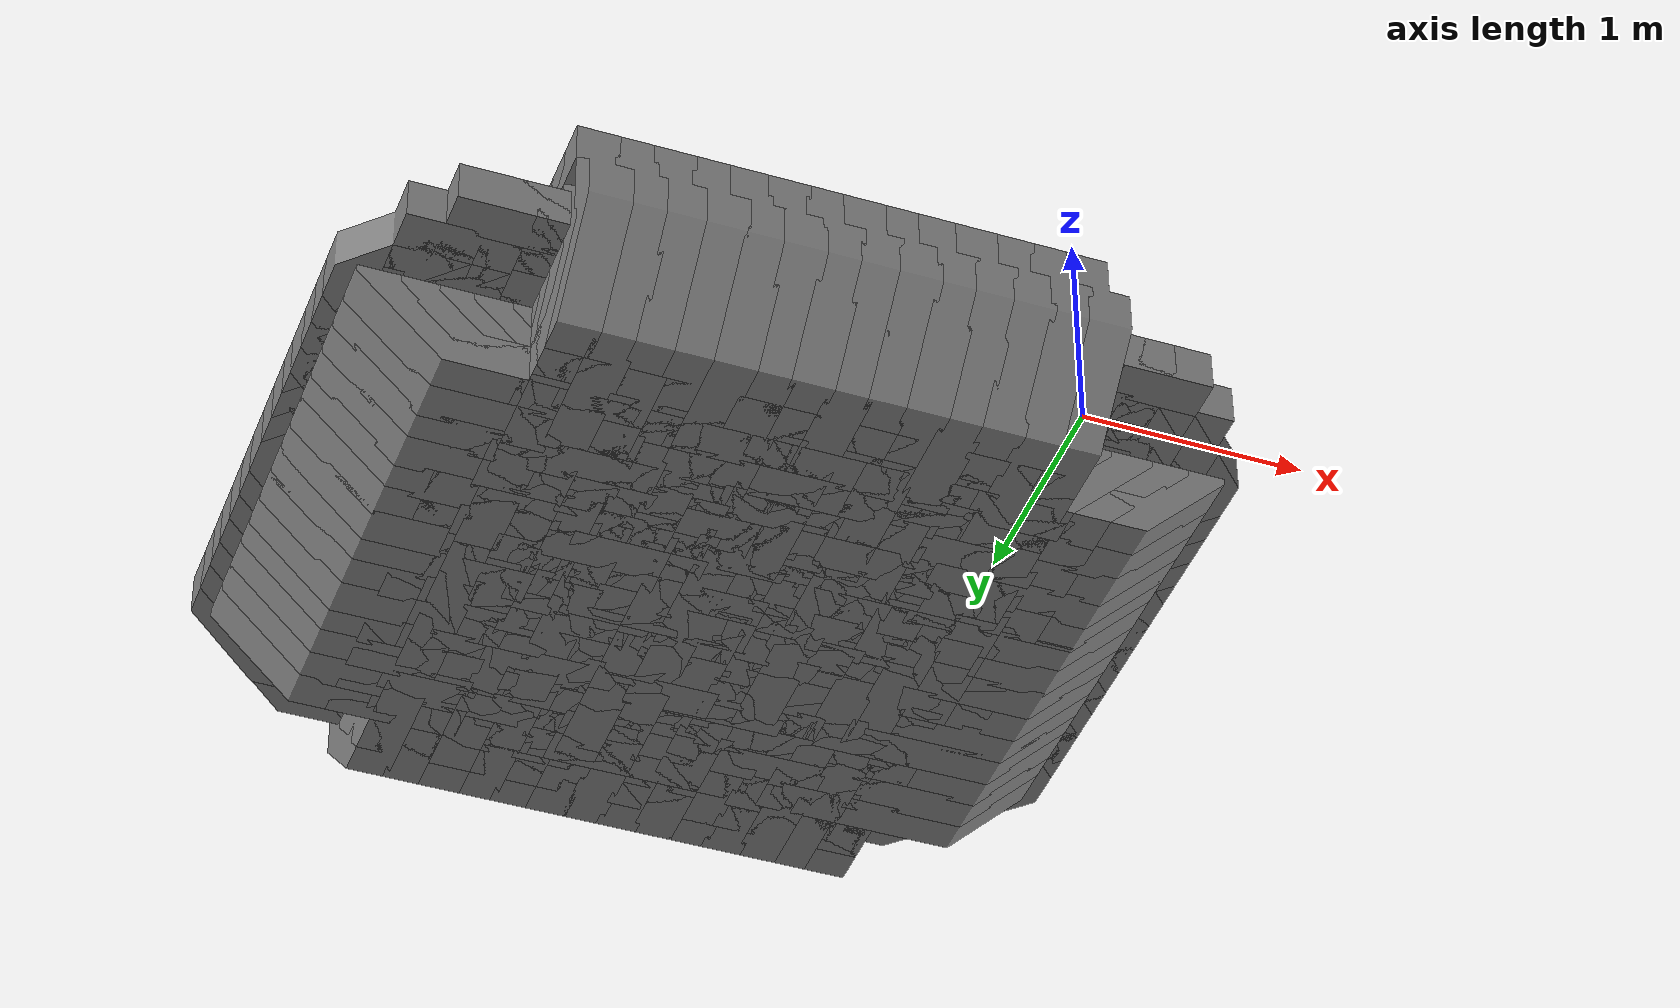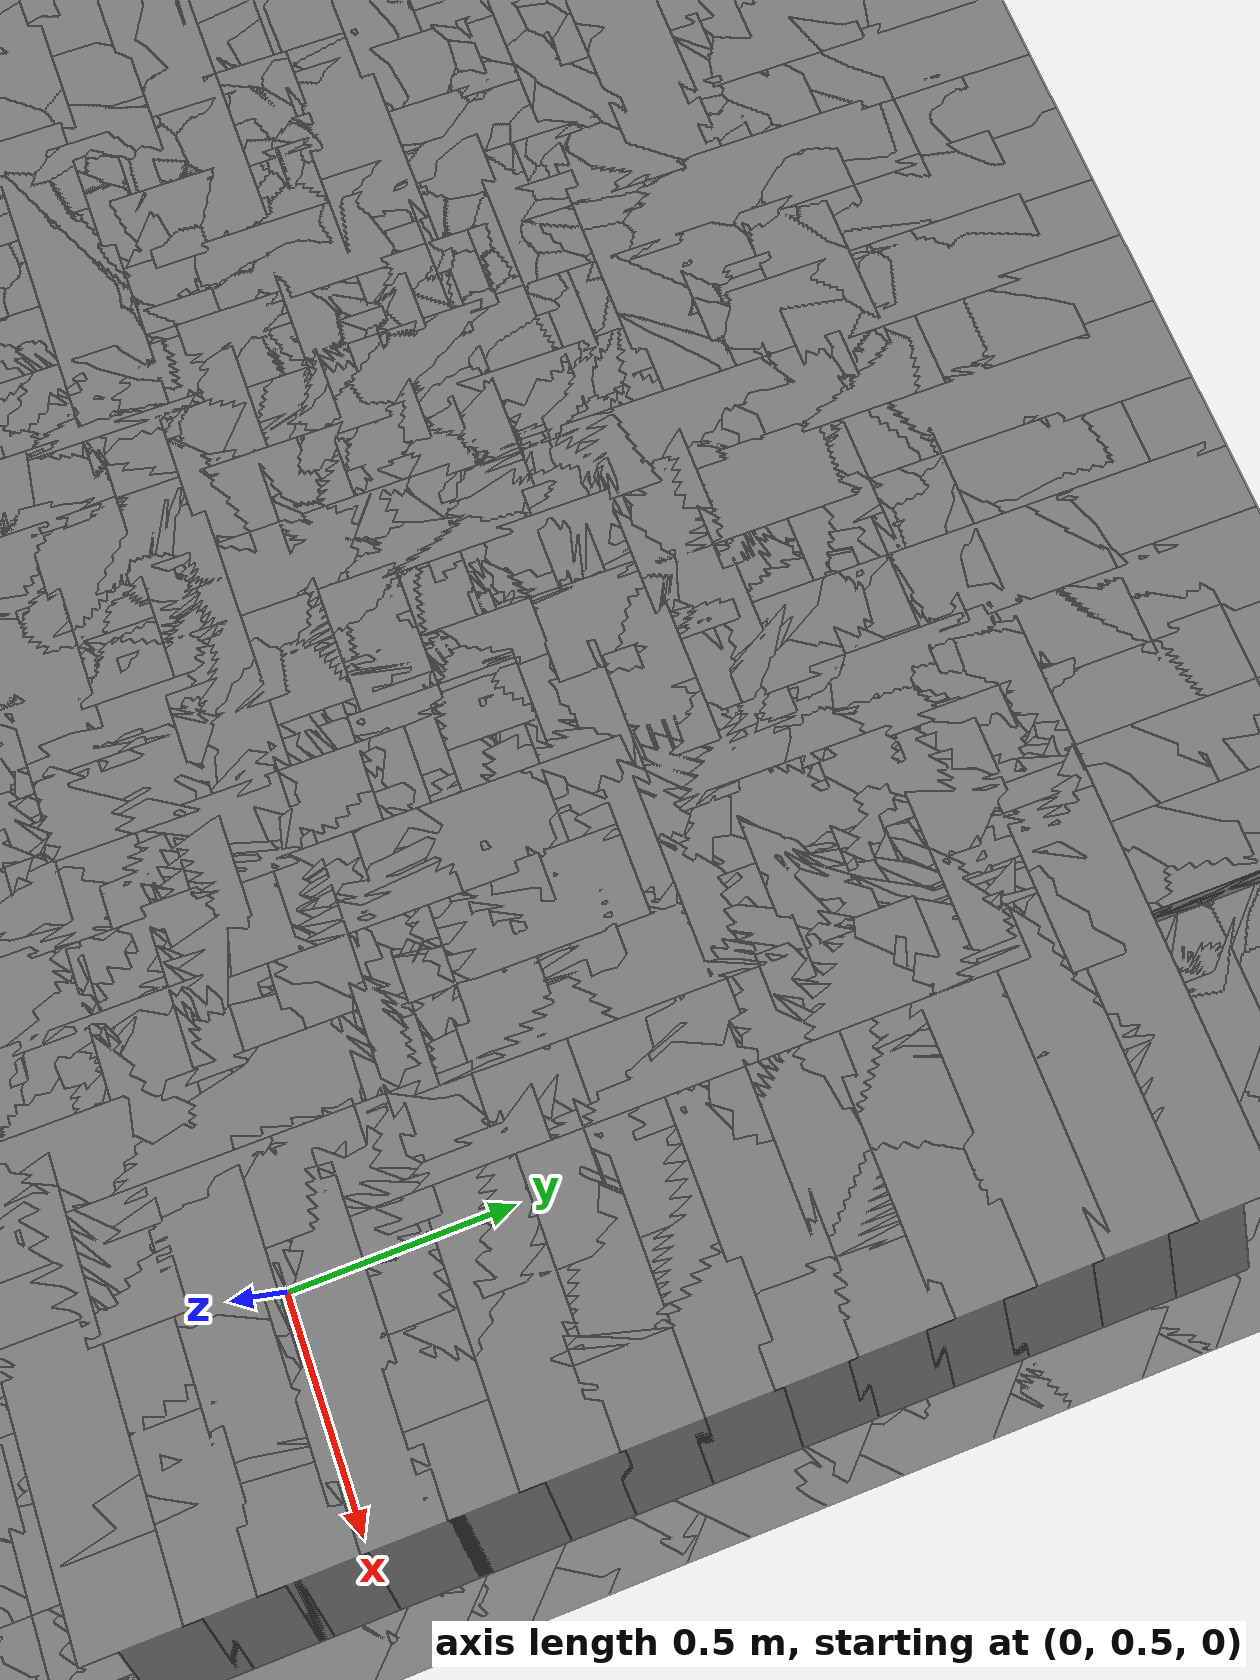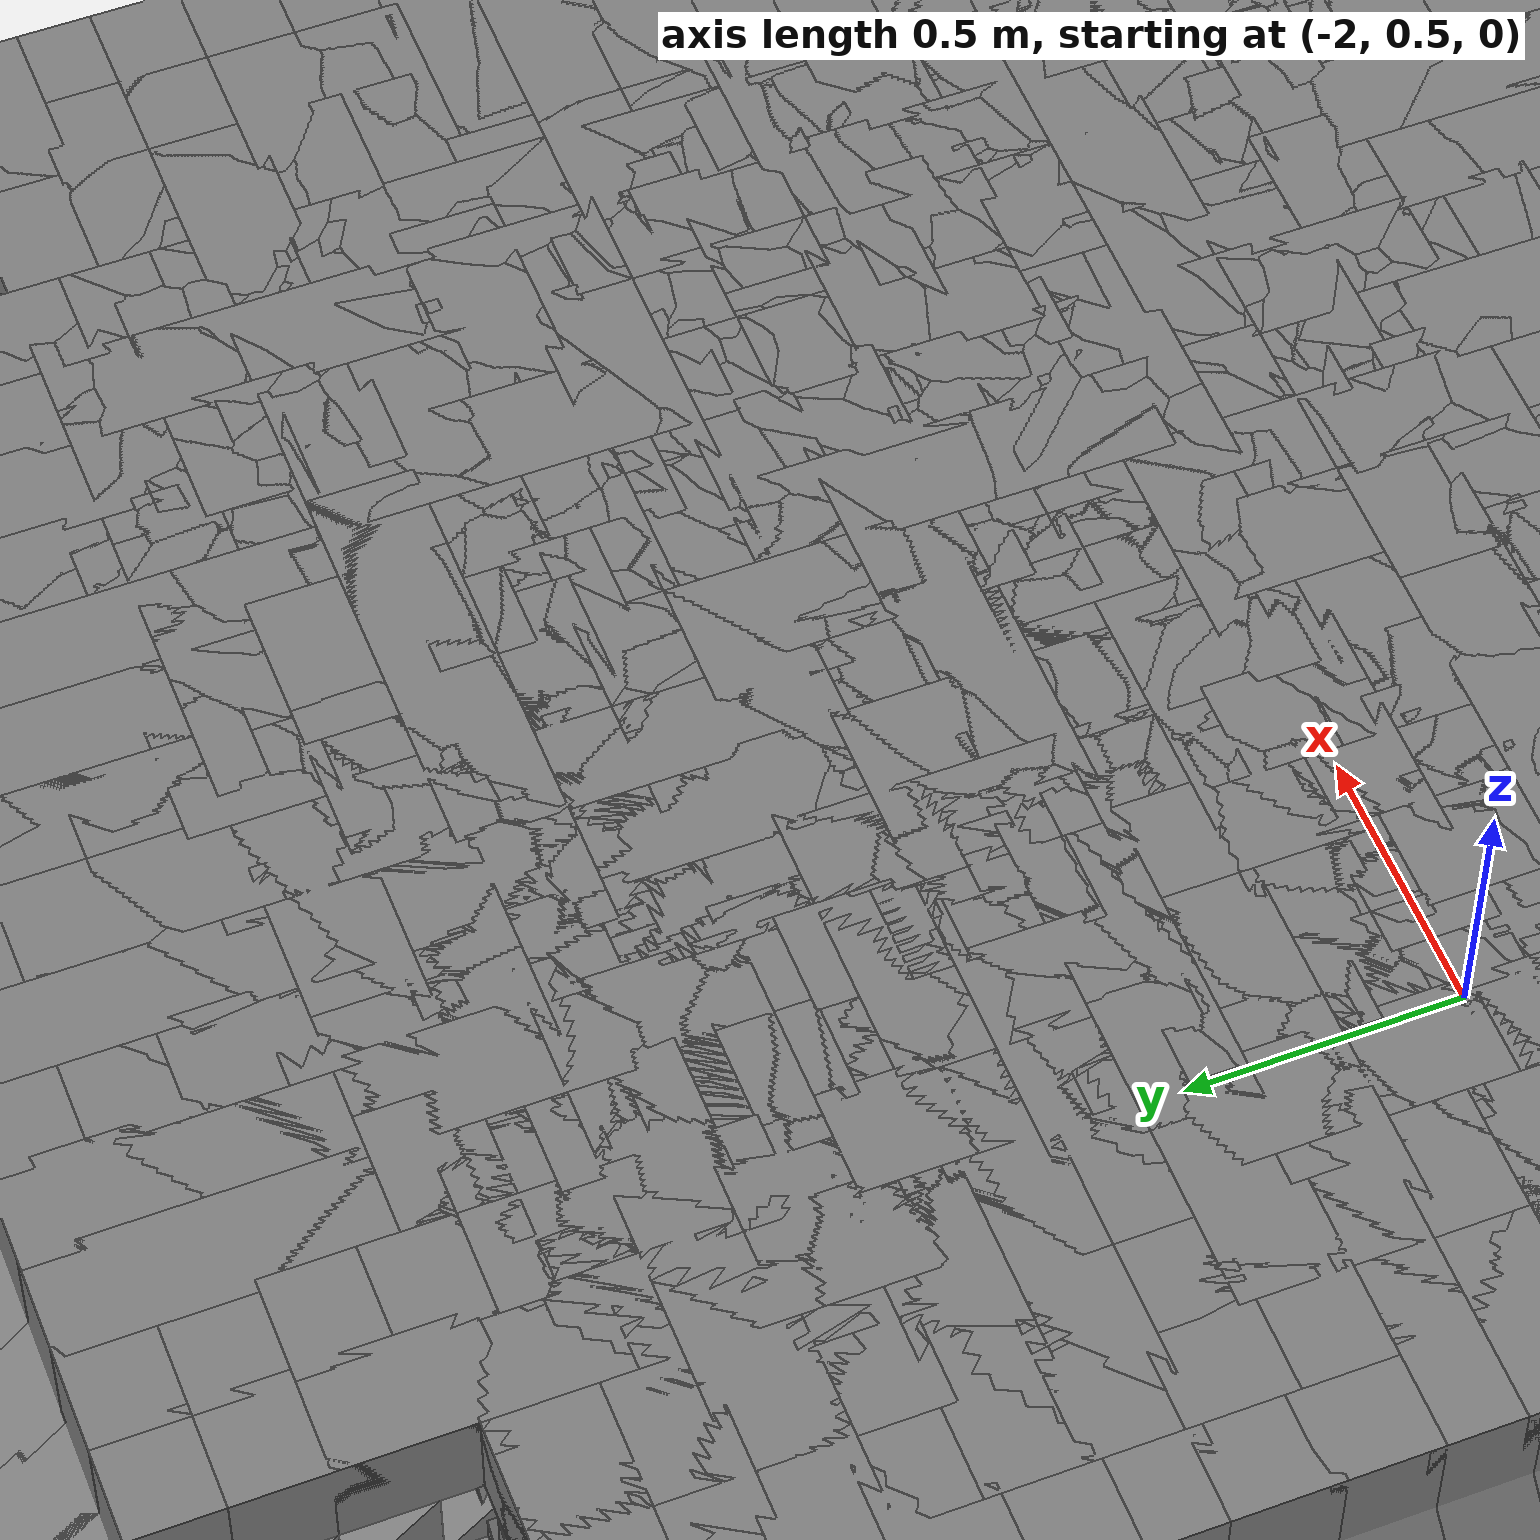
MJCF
<mujoco>
    <asset>
        <mesh file="wrecking-ball/link.obj" name="wrecking-ball/link"/>
    </asset>
    <worldbody>
        <body pos="-0.165 0.0 0" quat="-2.16489e-17 -0.707107 0.707107 2.16489e-17">
            <geom mesh="wrecking-ball/link" type="mesh" size="0.100000 0.100000 0.100000" density="7680.000000"/>
            <inertial mass="0"/>
        </body>
        <body pos="-0.165 0.08000000000000002 0" quat="0.707107 -2.16489e-17 -0.707107 -2.16489e-17">
            <geom mesh="wrecking-ball/link" type="mesh" size="0.100000 0.100000 0.100000" density="7680.000000"/>
        </body>
        <body pos="-0.33 0.0 0" quat="-2.16489e-17 -0.707107 0.707107 2.16489e-17">
            <geom mesh="wrecking-ball/link" type="mesh" size="0.100000 0.100000 0.100000" density="7680.000000"/>
            <inertial mass="0"/>
        </body>
        <body pos="-0.33 0.08000000000000002 0" quat="0.707107 -2.16489e-17 -0.707107 -2.16489e-17">
            <geom mesh="wrecking-ball/link" type="mesh" size="0.100000 0.100000 0.100000" density="7680.000000"/>
        </body>
        <body pos="-0.495 0.0 0" quat="-2.16489e-17 -0.707107 0.707107 2.16489e-17">
            <geom mesh="wrecking-ball/link" type="mesh" size="0.100000 0.100000 0.100000" density="7680.000000"/>
            <inertial mass="0"/>
        </body>
        <body pos="-0.495 0.08000000000000002 0" quat="0.707107 -2.16489e-17 -0.707107 -2.16489e-17">
            <geom mesh="wrecking-ball/link" type="mesh" size="0.100000 0.100000 0.100000" density="7680.000000"/>
        </body>
        <body pos="-0.66 0.0 0" quat="-2.16489e-17 -0.707107 0.707107 2.16489e-17">
            <geom mesh="wrecking-ball/link" type="mesh" size="0.100000 0.100000 0.100000" density="7680.000000"/>
            <inertial mass="0"/>
        </body>
        <body pos="-0.66 0.08000000000000002 0" quat="0.707107 -2.16489e-17 -0.707107 -2.16489e-17">
            <geom mesh="wrecking-ball/link" type="mesh" size="0.100000 0.100000 0.100000" density="7680.000000"/>
        </body>
        <body pos="-0.825 0.0 0" quat="-2.16489e-17 -0.707107 0.707107 2.16489e-17">
            <geom mesh="wrecking-ball/link" type="mesh" size="0.100000 0.100000 0.100000" density="7680.000000"/>
            <inertial mass="0"/>
        </body>
        <body pos="-0.825 0.08000000000000002 0" quat="0.707107 -2.16489e-17 -0.707107 -2.16489e-17">
            <geom mesh="wrecking-ball/link" type="mesh" size="0.100000 0.100000 0.100000" density="7680.000000"/>
        </body>
        <body pos="-0.99 0.0 0" quat="-2.16489e-17 -0.707107 0.707107 2.16489e-17">
            <geom mesh="wrecking-ball/link" type="mesh" size="0.100000 0.100000 0.100000" density="7680.000000"/>
            <inertial mass="0"/>
        </body>
        <body pos="-0.99 0.08000000000000002 0" quat="0.707107 -2.16489e-17 -0.707107 -2.16489e-17">
            <geom mesh="wrecking-ball/link" type="mesh" size="0.100000 0.100000 0.100000" density="7680.000000"/>
        </body>
        <body pos="-1.155 0.0 0" quat="-2.16489e-17 -0.707107 0.707107 2.16489e-17">
            <geom mesh="wrecking-ball/link" type="mesh" size="0.100000 0.100000 0.100000" density="7680.000000"/>
            <inertial mass="0"/>
        </body>
        <body pos="-1.155 0.08000000000000002 0" quat="0.707107 -2.16489e-17 -0.707107 -2.16489e-17">
            <geom mesh="wrecking-ball/link" type="mesh" size="0.100000 0.100000 0.100000" density="7680.000000"/>
        </body>
        <body pos="-1.32 0.0 0" quat="-2.16489e-17 -0.707107 0.707107 2.16489e-17">
            <geom mesh="wrecking-ball/link" type="mesh" size="0.100000 0.100000 0.100000" density="7680.000000"/>
            <inertial mass="0"/>
        </body>
        <body pos="-1.32 0.08000000000000002 0" quat="0.707107 -2.16489e-17 -0.707107 -2.16489e-17">
            <geom mesh="wrecking-ball/link" type="mesh" size="0.100000 0.100000 0.100000" density="7680.000000"/>
        </body>
        <body pos="-1.485 0.0 0" quat="-2.16489e-17 -0.707107 0.707107 2.16489e-17">
            <geom mesh="wrecking-ball/link" type="mesh" size="0.100000 0.100000 0.100000" density="7680.000000"/>
            <inertial mass="0"/>
        </body>
        <body pos="-1.485 0.08000000000000002 0" quat="0.707107 -2.16489e-17 -0.707107 -2.16489e-17">
            <geom mesh="wrecking-ball/link" type="mesh" size="0.100000 0.100000 0.100000" density="7680.000000"/>
        </body>
        <body pos="-1.65 0.0 0" quat="-2.16489e-17 -0.707107 0.707107 2.16489e-17">
            <geom mesh="wrecking-ball/link" type="mesh" size="0.100000 0.100000 0.100000" density="7680.000000"/>
            <inertial mass="0"/>
        </body>
        <body pos="-1.65 0.08000000000000002 0" quat="0.707107 -2.16489e-17 -0.707107 -2.16489e-17">
            <geom mesh="wrecking-ball/link" type="mesh" size="0.100000 0.100000 0.100000" density="7680.000000"/>
        </body>
        <body pos="-1.815 0.0 0" quat="-2.16489e-17 -0.707107 0.707107 2.16489e-17">
            <geom mesh="wrecking-ball/link" type="mesh" size="0.100000 0.100000 0.100000" density="7680.000000"/>
            <inertial mass="0"/>
        </body>
        <body pos="-1.815 0.08000000000000002 0" quat="0.707107 -2.16489e-17 -0.707107 -2.16489e-17">
            <geom mesh="wrecking-ball/link" type="mesh" size="0.100000 0.100000 0.100000" density="7680.000000"/>
        </body>
        <body pos="-1.98 0.0 0" quat="-2.16489e-17 -0.707107 0.707107 2.16489e-17">
            <geom mesh="wrecking-ball/link" type="mesh" size="0.100000 0.100000 0.100000" density="7680.000000"/>
            <inertial mass="0"/>
        </body>
        <body pos="-1.98 0.08000000000000002 0" quat="0.707107 -2.16489e-17 -0.707107 -2.16489e-17">
            <geom mesh="wrecking-ball/link" type="mesh" size="0.100000 0.100000 0.100000" density="7680.000000"/>
        </body>
        <body pos="-2.145 0.0 0" quat="-2.16489e-17 -0.707107 0.707107 2.16489e-17">
            <geom mesh="wrecking-ball/link" type="mesh" size="0.100000 0.100000 0.100000" density="7680.000000"/>
            <inertial mass="0"/>
        </body>
        <body pos="-2.145 0.08000000000000002 0" quat="0.707107 -2.16489e-17 -0.707107 -2.16489e-17">
            <geom mesh="wrecking-ball/link" type="mesh" size="0.100000 0.100000 0.100000" density="7680.000000"/>
        </body>
        <body pos="-2.31 0.0 0" quat="-2.16489e-17 -0.707107 0.707107 2.16489e-17">
            <geom mesh="wrecking-ball/link" type="mesh" size="0.100000 0.100000 0.100000" density="7680.000000"/>
            <inertial mass="0"/>
        </body>
        <body pos="-2.31 0.08000000000000002 0" quat="0.707107 -2.16489e-17 -0.707107 -2.16489e-17">
            <geom mesh="wrecking-ball/link" type="mesh" size="0.100000 0.100000 0.100000" density="7680.000000"/>
        </body>
        <body pos="-0 0.16000000000000003 0" quat="-2.16489e-17 -0.707107 0.707107 2.16489e-17">
            <geom mesh="wrecking-ball/link" type="mesh" size="0.100000 0.100000 0.100000" density="7680.000000"/>
            <inertial mass="0"/>
        </body>
        <body pos="-0.0825 0.16000000000000003 0" quat="-0.5 0.5 0.5 0.5">
            <geom mesh="wrecking-ball/link" type="mesh" size="0.100000 0.100000 0.100000" density="7680.000000"/>
        </body>
        <body pos="-0.165 0.16000000000000003 0" quat="-2.16489e-17 -0.707107 0.707107 2.16489e-17">
            <geom mesh="wrecking-ball/link" type="mesh" size="0.100000 0.100000 0.100000" density="7680.000000"/>
        </body>
        <body pos="-0.2475 0.16000000000000003 0" quat="-0.5 0.5 0.5 0.5">
            <geom mesh="wrecking-ball/link" type="mesh" size="0.100000 0.100000 0.100000" density="7680.000000"/>
        </body>
        <body pos="-0.165 0.24000000000000005 0" quat="0.707107 -2.16489e-17 -0.707107 -2.16489e-17">
            <geom mesh="wrecking-ball/link" type="mesh" size="0.100000 0.100000 0.100000" density="7680.000000"/>
        </body>
        <body pos="-0.33 0.16000000000000003 0" quat="-2.16489e-17 -0.707107 0.707107 2.16489e-17">
            <geom mesh="wrecking-ball/link" type="mesh" size="0.100000 0.100000 0.100000" density="7680.000000"/>
        </body>
        <body pos="-0.4125 0.16000000000000003 0" quat="-0.5 0.5 0.5 0.5">
            <geom mesh="wrecking-ball/link" type="mesh" size="0.100000 0.100000 0.100000" density="7680.000000"/>
        </body>
        <body pos="-0.33 0.24000000000000005 0" quat="0.707107 -2.16489e-17 -0.707107 -2.16489e-17">
            <geom mesh="wrecking-ball/link" type="mesh" size="0.100000 0.100000 0.100000" density="7680.000000"/>
        </body>
        <body pos="-0.495 0.16000000000000003 0" quat="-2.16489e-17 -0.707107 0.707107 2.16489e-17">
            <geom mesh="wrecking-ball/link" type="mesh" size="0.100000 0.100000 0.100000" density="7680.000000"/>
        </body>
        <body pos="-0.5775 0.16000000000000003 0" quat="-0.5 0.5 0.5 0.5">
            <geom mesh="wrecking-ball/link" type="mesh" size="0.100000 0.100000 0.100000" density="7680.000000"/>
        </body>
        <body pos="-0.495 0.24000000000000005 0" quat="0.707107 -2.16489e-17 -0.707107 -2.16489e-17">
            <geom mesh="wrecking-ball/link" type="mesh" size="0.100000 0.100000 0.100000" density="7680.000000"/>
        </body>
        <body pos="-0.66 0.16000000000000003 0" quat="-2.16489e-17 -0.707107 0.707107 2.16489e-17">
            <geom mesh="wrecking-ball/link" type="mesh" size="0.100000 0.100000 0.100000" density="7680.000000"/>
        </body>
        <body pos="-0.7425 0.16000000000000003 0" quat="-0.5 0.5 0.5 0.5">
            <geom mesh="wrecking-ball/link" type="mesh" size="0.100000 0.100000 0.100000" density="7680.000000"/>
        </body>
        <body pos="-0.66 0.24000000000000005 0" quat="0.707107 -2.16489e-17 -0.707107 -2.16489e-17">
            <geom mesh="wrecking-ball/link" type="mesh" size="0.100000 0.100000 0.100000" density="7680.000000"/>
        </body>
        <body pos="-0.825 0.16000000000000003 0" quat="-2.16489e-17 -0.707107 0.707107 2.16489e-17">
            <geom mesh="wrecking-ball/link" type="mesh" size="0.100000 0.100000 0.100000" density="7680.000000"/>
        </body>
        <body pos="-0.9075 0.16000000000000003 0" quat="-0.5 0.5 0.5 0.5">
            <geom mesh="wrecking-ball/link" type="mesh" size="0.100000 0.100000 0.100000" density="7680.000000"/>
        </body>
        <body pos="-0.825 0.24000000000000005 0" quat="0.707107 -2.16489e-17 -0.707107 -2.16489e-17">
            <geom mesh="wrecking-ball/link" type="mesh" size="0.100000 0.100000 0.100000" density="7680.000000"/>
        </body>
        <body pos="-0.99 0.16000000000000003 0" quat="-2.16489e-17 -0.707107 0.707107 2.16489e-17">
            <geom mesh="wrecking-ball/link" type="mesh" size="0.100000 0.100000 0.100000" density="7680.000000"/>
        </body>
        <body pos="-1.0725 0.16000000000000003 0" quat="-0.5 0.5 0.5 0.5">
            <geom mesh="wrecking-ball/link" type="mesh" size="0.100000 0.100000 0.100000" density="7680.000000"/>
        </body>
        <body pos="-0.99 0.24000000000000005 0" quat="0.707107 -2.16489e-17 -0.707107 -2.16489e-17">
            <geom mesh="wrecking-ball/link" type="mesh" size="0.100000 0.100000 0.100000" density="7680.000000"/>
        </body>
        <body pos="-1.155 0.16000000000000003 0" quat="-2.16489e-17 -0.707107 0.707107 2.16489e-17">
            <geom mesh="wrecking-ball/link" type="mesh" size="0.100000 0.100000 0.100000" density="7680.000000"/>
        </body>
        <body pos="-1.2375 0.16000000000000003 0" quat="-0.5 0.5 0.5 0.5">
            <geom mesh="wrecking-ball/link" type="mesh" size="0.100000 0.100000 0.100000" density="7680.000000"/>
        </body>
        <body pos="-1.155 0.24000000000000005 0" quat="0.707107 -2.16489e-17 -0.707107 -2.16489e-17">
            <geom mesh="wrecking-ball/link" type="mesh" size="0.100000 0.100000 0.100000" density="7680.000000"/>
        </body>
        <body pos="-1.32 0.16000000000000003 0" quat="-2.16489e-17 -0.707107 0.707107 2.16489e-17">
            <geom mesh="wrecking-ball/link" type="mesh" size="0.100000 0.100000 0.100000" density="7680.000000"/>
        </body>
        <body pos="-1.4025 0.16000000000000003 0" quat="-0.5 0.5 0.5 0.5">
            <geom mesh="wrecking-ball/link" type="mesh" size="0.100000 0.100000 0.100000" density="7680.000000"/>
        </body>
        <body pos="-1.32 0.24000000000000005 0" quat="0.707107 -2.16489e-17 -0.707107 -2.16489e-17">
            <geom mesh="wrecking-ball/link" type="mesh" size="0.100000 0.100000 0.100000" density="7680.000000"/>
        </body>
        <body pos="-1.485 0.16000000000000003 0" quat="-2.16489e-17 -0.707107 0.707107 2.16489e-17">
            <geom mesh="wrecking-ball/link" type="mesh" size="0.100000 0.100000 0.100000" density="7680.000000"/>
        </body>
        <body pos="-1.5675 0.16000000000000003 0" quat="-0.5 0.5 0.5 0.5">
            <geom mesh="wrecking-ball/link" type="mesh" size="0.100000 0.100000 0.100000" density="7680.000000"/>
        </body>
        <body pos="-1.485 0.24000000000000005 0" quat="0.707107 -2.16489e-17 -0.707107 -2.16489e-17">
            <geom mesh="wrecking-ball/link" type="mesh" size="0.100000 0.100000 0.100000" density="7680.000000"/>
        </body>
        <body pos="-1.65 0.16000000000000003 0" quat="-2.16489e-17 -0.707107 0.707107 2.16489e-17">
            <geom mesh="wrecking-ball/link" type="mesh" size="0.100000 0.100000 0.100000" density="7680.000000"/>
        </body>
        <body pos="-1.7325 0.16000000000000003 0" quat="-0.5 0.5 0.5 0.5">
            <geom mesh="wrecking-ball/link" type="mesh" size="0.100000 0.100000 0.100000" density="7680.000000"/>
        </body>
        <body pos="-1.65 0.24000000000000005 0" quat="0.707107 -2.16489e-17 -0.707107 -2.16489e-17">
            <geom mesh="wrecking-ball/link" type="mesh" size="0.100000 0.100000 0.100000" density="7680.000000"/>
        </body>
        <body pos="-1.815 0.16000000000000003 0" quat="-2.16489e-17 -0.707107 0.707107 2.16489e-17">
            <geom mesh="wrecking-ball/link" type="mesh" size="0.100000 0.100000 0.100000" density="7680.000000"/>
        </body>
        <body pos="-1.8975 0.16000000000000003 0" quat="-0.5 0.5 0.5 0.5">
            <geom mesh="wrecking-ball/link" type="mesh" size="0.100000 0.100000 0.100000" density="7680.000000"/>
        </body>
        <body pos="-1.815 0.24000000000000005 0" quat="0.707107 -2.16489e-17 -0.707107 -2.16489e-17">
            <geom mesh="wrecking-ball/link" type="mesh" size="0.100000 0.100000 0.100000" density="7680.000000"/>
        </body>
        <body pos="-1.98 0.16000000000000003 0" quat="-2.16489e-17 -0.707107 0.707107 2.16489e-17">
            <geom mesh="wrecking-ball/link" type="mesh" size="0.100000 0.100000 0.100000" density="7680.000000"/>
        </body>
        <body pos="-2.0625 0.16000000000000003 0" quat="-0.5 0.5 0.5 0.5">
            <geom mesh="wrecking-ball/link" type="mesh" size="0.100000 0.100000 0.100000" density="7680.000000"/>
        </body>
        <body pos="-1.98 0.24000000000000005 0" quat="0.707107 -2.16489e-17 -0.707107 -2.16489e-17">
            <geom mesh="wrecking-ball/link" type="mesh" size="0.100000 0.100000 0.100000" density="7680.000000"/>
        </body>
        <body pos="-2.145 0.16000000000000003 0" quat="-2.16489e-17 -0.707107 0.707107 2.16489e-17">
            <geom mesh="wrecking-ball/link" type="mesh" size="0.100000 0.100000 0.100000" density="7680.000000"/>
        </body>
        <body pos="-2.2275 0.16000000000000003 0" quat="-0.5 0.5 0.5 0.5">
            <geom mesh="wrecking-ball/link" type="mesh" size="0.100000 0.100000 0.100000" density="7680.000000"/>
        </body>
        <body pos="-2.145 0.24000000000000005 0" quat="0.707107 -2.16489e-17 -0.707107 -2.16489e-17">
            <geom mesh="wrecking-ball/link" type="mesh" size="0.100000 0.100000 0.100000" density="7680.000000"/>
        </body>
        <body pos="-2.31 0.16000000000000003 0" quat="-2.16489e-17 -0.707107 0.707107 2.16489e-17">
            <geom mesh="wrecking-ball/link" type="mesh" size="0.100000 0.100000 0.100000" density="7680.000000"/>
        </body>
        <body pos="-2.3925 0.16000000000000003 0" quat="-0.5 0.5 0.5 0.5">
            <geom mesh="wrecking-ball/link" type="mesh" size="0.100000 0.100000 0.100000" density="7680.000000"/>
        </body>
        <body pos="-2.31 0.24000000000000005 0" quat="0.707107 -2.16489e-17 -0.707107 -2.16489e-17">
            <geom mesh="wrecking-ball/link" type="mesh" size="0.100000 0.100000 0.100000" density="7680.000000"/>
        </body>
        <body pos="-2.475 0.16000000000000003 0" quat="-2.16489e-17 -0.707107 0.707107 2.16489e-17">
            <geom mesh="wrecking-ball/link" type="mesh" size="0.100000 0.100000 0.100000" density="7680.000000"/>
            <inertial mass="0"/>
        </body>
        <body pos="-0 0.32000000000000006 0" quat="-2.16489e-17 -0.707107 0.707107 2.16489e-17">
            <geom mesh="wrecking-ball/link" type="mesh" size="0.100000 0.100000 0.100000" density="7680.000000"/>
            <inertial mass="0"/>
        </body>
        <body pos="-0.0825 0.32000000000000006 0" quat="-0.5 0.5 0.5 0.5">
            <geom mesh="wrecking-ball/link" type="mesh" size="0.100000 0.100000 0.100000" density="7680.000000"/>
        </body>
        <body pos="-0.165 0.32000000000000006 0" quat="-2.16489e-17 -0.707107 0.707107 2.16489e-17">
            <geom mesh="wrecking-ball/link" type="mesh" size="0.100000 0.100000 0.100000" density="7680.000000"/>
        </body>
        <body pos="-0.2475 0.32000000000000006 0" quat="-0.5 0.5 0.5 0.5">
            <geom mesh="wrecking-ball/link" type="mesh" size="0.100000 0.100000 0.100000" density="7680.000000"/>
        </body>
        <body pos="-0.165 0.4000000000000001 0" quat="0.707107 -2.16489e-17 -0.707107 -2.16489e-17">
            <geom mesh="wrecking-ball/link" type="mesh" size="0.100000 0.100000 0.100000" density="7680.000000"/>
        </body>
        <body pos="-0.33 0.32000000000000006 0" quat="-2.16489e-17 -0.707107 0.707107 2.16489e-17">
            <geom mesh="wrecking-ball/link" type="mesh" size="0.100000 0.100000 0.100000" density="7680.000000"/>
        </body>
        <body pos="-0.4125 0.32000000000000006 0" quat="-0.5 0.5 0.5 0.5">
            <geom mesh="wrecking-ball/link" type="mesh" size="0.100000 0.100000 0.100000" density="7680.000000"/>
        </body>
        <body pos="-0.33 0.4000000000000001 0" quat="0.707107 -2.16489e-17 -0.707107 -2.16489e-17">
            <geom mesh="wrecking-ball/link" type="mesh" size="0.100000 0.100000 0.100000" density="7680.000000"/>
        </body>
        <body pos="-0.495 0.32000000000000006 0" quat="-2.16489e-17 -0.707107 0.707107 2.16489e-17">
            <geom mesh="wrecking-ball/link" type="mesh" size="0.100000 0.100000 0.100000" density="7680.000000"/>
        </body>
        <body pos="-0.5775 0.32000000000000006 0" quat="-0.5 0.5 0.5 0.5">
            <geom mesh="wrecking-ball/link" type="mesh" size="0.100000 0.100000 0.100000" density="7680.000000"/>
        </body>
        <body pos="-0.495 0.4000000000000001 0" quat="0.707107 -2.16489e-17 -0.707107 -2.16489e-17">
            <geom mesh="wrecking-ball/link" type="mesh" size="0.100000 0.100000 0.100000" density="7680.000000"/>
        </body>
        <body pos="-0.66 0.32000000000000006 0" quat="-2.16489e-17 -0.707107 0.707107 2.16489e-17">
            <geom mesh="wrecking-ball/link" type="mesh" size="0.100000 0.100000 0.100000" density="7680.000000"/>
        </body>
        <body pos="-0.7425 0.32000000000000006 0" quat="-0.5 0.5 0.5 0.5">
            <geom mesh="wrecking-ball/link" type="mesh" size="0.100000 0.100000 0.100000" density="7680.000000"/>
        </body>
        <body pos="-0.66 0.4000000000000001 0" quat="0.707107 -2.16489e-17 -0.707107 -2.16489e-17">
            <geom mesh="wrecking-ball/link" type="mesh" size="0.100000 0.100000 0.100000" density="7680.000000"/>
        </body>
        <body pos="-0.825 0.32000000000000006 0" quat="-2.16489e-17 -0.707107 0.707107 2.16489e-17">
            <geom mesh="wrecking-ball/link" type="mesh" size="0.100000 0.100000 0.100000" density="7680.000000"/>
        </body>
        <body pos="-0.9075 0.32000000000000006 0" quat="-0.5 0.5 0.5 0.5">
            <geom mesh="wrecking-ball/link" type="mesh" size="0.100000 0.100000 0.100000" density="7680.000000"/>
        </body>
        <body pos="-0.825 0.4000000000000001 0" quat="0.707107 -2.16489e-17 -0.707107 -2.16489e-17">
            <geom mesh="wrecking-ball/link" type="mesh" size="0.100000 0.100000 0.100000" density="7680.000000"/>
        </body>
        <body pos="-0.99 0.32000000000000006 0" quat="-2.16489e-17 -0.707107 0.707107 2.16489e-17">
            <geom mesh="wrecking-ball/link" type="mesh" size="0.100000 0.100000 0.100000" density="7680.000000"/>
        </body>
        <body pos="-1.0725 0.32000000000000006 0" quat="-0.5 0.5 0.5 0.5">
            <geom mesh="wrecking-ball/link" type="mesh" size="0.100000 0.100000 0.100000" density="7680.000000"/>
        </body>
        <body pos="-0.99 0.4000000000000001 0" quat="0.707107 -2.16489e-17 -0.707107 -2.16489e-17">
            <geom mesh="wrecking-ball/link" type="mesh" size="0.100000 0.100000 0.100000" density="7680.000000"/>
        </body>
        <body pos="-1.155 0.32000000000000006 0" quat="-2.16489e-17 -0.707107 0.707107 2.16489e-17">
            <geom mesh="wrecking-ball/link" type="mesh" size="0.100000 0.100000 0.100000" density="7680.000000"/>
        </body>
        <body pos="-1.2375 0.32000000000000006 0" quat="-0.5 0.5 0.5 0.5">
            <geom mesh="wrecking-ball/link" type="mesh" size="0.100000 0.100000 0.100000" density="7680.000000"/>
        </body>
        <body pos="-1.155 0.4000000000000001 0" quat="0.707107 -2.16489e-17 -0.707107 -2.16489e-17">
            <geom mesh="wrecking-ball/link" type="mesh" size="0.100000 0.100000 0.100000" density="7680.000000"/>
        </body>
        <body pos="-1.32 0.32000000000000006 0" quat="-2.16489e-17 -0.707107 0.707107 2.16489e-17">
            <geom mesh="wrecking-ball/link" type="mesh" size="0.100000 0.100000 0.100000" density="7680.000000"/>
        </body>
        <body pos="-1.4025 0.32000000000000006 0" quat="-0.5 0.5 0.5 0.5">
            <geom mesh="wrecking-ball/link" type="mesh" size="0.100000 0.100000 0.100000" density="7680.000000"/>
        </body>
        <body pos="-1.32 0.4000000000000001 0" quat="0.707107 -2.16489e-17 -0.707107 -2.16489e-17">
            <geom mesh="wrecking-ball/link" type="mesh" size="0.100000 0.100000 0.100000" density="7680.000000"/>
        </body>
        <body pos="-1.485 0.32000000000000006 0" quat="-2.16489e-17 -0.707107 0.707107 2.16489e-17">
            <geom mesh="wrecking-ball/link" type="mesh" size="0.100000 0.100000 0.100000" density="7680.000000"/>
        </body>
        <body pos="-1.5675 0.32000000000000006 0" quat="-0.5 0.5 0.5 0.5">
            <geom mesh="wrecking-ball/link" type="mesh" size="0.100000 0.100000 0.100000" density="7680.000000"/>
        </body>
        <body pos="-1.485 0.4000000000000001 0" quat="0.707107 -2.16489e-17 -0.707107 -2.16489e-17">
            <geom mesh="wrecking-ball/link" type="mesh" size="0.100000 0.100000 0.100000" density="7680.000000"/>
        </body>
        <body pos="-1.65 0.32000000000000006 0" quat="-2.16489e-17 -0.707107 0.707107 2.16489e-17">
            <geom mesh="wrecking-ball/link" type="mesh" size="0.100000 0.100000 0.100000" density="7680.000000"/>
        </body>
        <body pos="-1.7325 0.32000000000000006 0" quat="-0.5 0.5 0.5 0.5">
            <geom mesh="wrecking-ball/link" type="mesh" size="0.100000 0.100000 0.100000" density="7680.000000"/>
        </body>
        <body pos="-1.65 0.4000000000000001 0" quat="0.707107 -2.16489e-17 -0.707107 -2.16489e-17">
            <geom mesh="wrecking-ball/link" type="mesh" size="0.100000 0.100000 0.100000" density="7680.000000"/>
        </body>
        <body pos="-1.815 0.32000000000000006 0" quat="-2.16489e-17 -0.707107 0.707107 2.16489e-17">
            <geom mesh="wrecking-ball/link" type="mesh" size="0.100000 0.100000 0.100000" density="7680.000000"/>
        </body>
        <body pos="-1.8975 0.32000000000000006 0" quat="-0.5 0.5 0.5 0.5">
            <geom mesh="wrecking-ball/link" type="mesh" size="0.100000 0.100000 0.100000" density="7680.000000"/>
        </body>
        <body pos="-1.815 0.4000000000000001 0" quat="0.707107 -2.16489e-17 -0.707107 -2.16489e-17">
            <geom mesh="wrecking-ball/link" type="mesh" size="0.100000 0.100000 0.100000" density="7680.000000"/>
        </body>
        <body pos="-1.98 0.32000000000000006 0" quat="-2.16489e-17 -0.707107 0.707107 2.16489e-17">
            <geom mesh="wrecking-ball/link" type="mesh" size="0.100000 0.100000 0.100000" density="7680.000000"/>
        </body>
        <body pos="-2.0625 0.32000000000000006 0" quat="-0.5 0.5 0.5 0.5">
            <geom mesh="wrecking-ball/link" type="mesh" size="0.100000 0.100000 0.100000" density="7680.000000"/>
        </body>
        <body pos="-1.98 0.4000000000000001 0" quat="0.707107 -2.16489e-17 -0.707107 -2.16489e-17">
            <geom mesh="wrecking-ball/link" type="mesh" size="0.100000 0.100000 0.100000" density="7680.000000"/>
        </body>
        <body pos="-2.145 0.32000000000000006 0" quat="-2.16489e-17 -0.707107 0.707107 2.16489e-17">
            <geom mesh="wrecking-ball/link" type="mesh" size="0.100000 0.100000 0.100000" density="7680.000000"/>
        </body>
        <body pos="-2.2275 0.32000000000000006 0" quat="-0.5 0.5 0.5 0.5">
            <geom mesh="wrecking-ball/link" type="mesh" size="0.100000 0.100000 0.100000" density="7680.000000"/>
        </body>
        <body pos="-2.145 0.4000000000000001 0" quat="0.707107 -2.16489e-17 -0.707107 -2.16489e-17">
            <geom mesh="wrecking-ball/link" type="mesh" size="0.100000 0.100000 0.100000" density="7680.000000"/>
        </body>
        <body pos="-2.31 0.32000000000000006 0" quat="-2.16489e-17 -0.707107 0.707107 2.16489e-17">
            <geom mesh="wrecking-ball/link" type="mesh" size="0.100000 0.100000 0.100000" density="7680.000000"/>
        </body>
        <body pos="-2.3925 0.32000000000000006 0" quat="-0.5 0.5 0.5 0.5">
            <geom mesh="wrecking-ball/link" type="mesh" size="0.100000 0.100000 0.100000" density="7680.000000"/>
        </body>
        <body pos="-2.31 0.4000000000000001 0" quat="0.707107 -2.16489e-17 -0.707107 -2.16489e-17">
            <geom mesh="wrecking-ball/link" type="mesh" size="0.100000 0.100000 0.100000" density="7680.000000"/>
        </body>
        <body pos="-2.475 0.32000000000000006 0" quat="-2.16489e-17 -0.707107 0.707107 2.16489e-17">
            <geom mesh="wrecking-ball/link" type="mesh" size="0.100000 0.100000 0.100000" density="7680.000000"/>
            <inertial mass="0"/>
        </body>
        <body pos="-0 0.4800000000000001 0" quat="-2.16489e-17 -0.707107 0.707107 2.16489e-17">
            <geom mesh="wrecking-ball/link" type="mesh" size="0.100000 0.100000 0.100000" density="7680.000000"/>
            <inertial mass="0"/>
        </body>
        <body pos="-0.0825 0.4800000000000001 0" quat="-0.5 0.5 0.5 0.5">
            <geom mesh="wrecking-ball/link" type="mesh" size="0.100000 0.100000 0.100000" density="7680.000000"/>
        </body>
        <body pos="-0.165 0.4800000000000001 0" quat="-2.16489e-17 -0.707107 0.707107 2.16489e-17">
            <geom mesh="wrecking-ball/link" type="mesh" size="0.100000 0.100000 0.100000" density="7680.000000"/>
        </body>
        <body pos="-0.2475 0.4800000000000001 0" quat="-0.5 0.5 0.5 0.5">
            <geom mesh="wrecking-ball/link" type="mesh" size="0.100000 0.100000 0.100000" density="7680.000000"/>
        </body>
        <body pos="-0.165 0.56 0" quat="0.707107 -2.16489e-17 -0.707107 -2.16489e-17">
            <geom mesh="wrecking-ball/link" type="mesh" size="0.100000 0.100000 0.100000" density="7680.000000"/>
        </body>
        <body pos="-0.33 0.4800000000000001 0" quat="-2.16489e-17 -0.707107 0.707107 2.16489e-17">
            <geom mesh="wrecking-ball/link" type="mesh" size="0.100000 0.100000 0.100000" density="7680.000000"/>
        </body>
        <body pos="-0.4125 0.4800000000000001 0" quat="-0.5 0.5 0.5 0.5">
            <geom mesh="wrecking-ball/link" type="mesh" size="0.100000 0.100000 0.100000" density="7680.000000"/>
        </body>
        <body pos="-0.33 0.56 0" quat="0.707107 -2.16489e-17 -0.707107 -2.16489e-17">
            <geom mesh="wrecking-ball/link" type="mesh" size="0.100000 0.100000 0.100000" density="7680.000000"/>
        </body>
        <body pos="-0.495 0.4800000000000001 0" quat="-2.16489e-17 -0.707107 0.707107 2.16489e-17">
            <geom mesh="wrecking-ball/link" type="mesh" size="0.100000 0.100000 0.100000" density="7680.000000"/>
        </body>
        <body pos="-0.5775 0.4800000000000001 0" quat="-0.5 0.5 0.5 0.5">
            <geom mesh="wrecking-ball/link" type="mesh" size="0.100000 0.100000 0.100000" density="7680.000000"/>
        </body>
        <body pos="-0.495 0.56 0" quat="0.707107 -2.16489e-17 -0.707107 -2.16489e-17">
            <geom mesh="wrecking-ball/link" type="mesh" size="0.100000 0.100000 0.100000" density="7680.000000"/>
        </body>
        <body pos="-0.66 0.4800000000000001 0" quat="-2.16489e-17 -0.707107 0.707107 2.16489e-17">
            <geom mesh="wrecking-ball/link" type="mesh" size="0.100000 0.100000 0.100000" density="7680.000000"/>
        </body>
        <body pos="-0.7425 0.4800000000000001 0" quat="-0.5 0.5 0.5 0.5">
            <geom mesh="wrecking-ball/link" type="mesh" size="0.100000 0.100000 0.100000" density="7680.000000"/>
        </body>
        <body pos="-0.66 0.56 0" quat="0.707107 -2.16489e-17 -0.707107 -2.16489e-17">
            <geom mesh="wrecking-ball/link" type="mesh" size="0.100000 0.100000 0.100000" density="7680.000000"/>
        </body>
        <body pos="-0.825 0.4800000000000001 0" quat="-2.16489e-17 -0.707107 0.707107 2.16489e-17">
            <geom mesh="wrecking-ball/link" type="mesh" size="0.100000 0.100000 0.100000" density="7680.000000"/>
        </body>
        <body pos="-0.9075 0.4800000000000001 0" quat="-0.5 0.5 0.5 0.5">
            <geom mesh="wrecking-ball/link" type="mesh" size="0.100000 0.100000 0.100000" density="7680.000000"/>
        </body>
        <body pos="-0.825 0.56 0" quat="0.707107 -2.16489e-17 -0.707107 -2.16489e-17">
            <geom mesh="wrecking-ball/link" type="mesh" size="0.100000 0.100000 0.100000" density="7680.000000"/>
        </body>
        <body pos="-0.99 0.4800000000000001 0" quat="-2.16489e-17 -0.707107 0.707107 2.16489e-17">
            <geom mesh="wrecking-ball/link" type="mesh" size="0.100000 0.100000 0.100000" density="7680.000000"/>
        </body>
        <body pos="-1.0725 0.4800000000000001 0" quat="-0.5 0.5 0.5 0.5">
            <geom mesh="wrecking-ball/link" type="mesh" size="0.100000 0.100000 0.100000" density="7680.000000"/>
        </body>
        <body pos="-0.99 0.56 0" quat="0.707107 -2.16489e-17 -0.707107 -2.16489e-17">
            <geom mesh="wrecking-ball/link" type="mesh" size="0.100000 0.100000 0.100000" density="7680.000000"/>
        </body>
        <body pos="-1.155 0.4800000000000001 0" quat="-2.16489e-17 -0.707107 0.707107 2.16489e-17">
            <geom mesh="wrecking-ball/link" type="mesh" size="0.100000 0.100000 0.100000" density="7680.000000"/>
        </body>
        <body pos="-1.2375 0.4800000000000001 0" quat="-0.5 0.5 0.5 0.5">
            <geom mesh="wrecking-ball/link" type="mesh" size="0.100000 0.100000 0.100000" density="7680.000000"/>
        </body>
        <body pos="-1.155 0.56 0" quat="0.707107 -2.16489e-17 -0.707107 -2.16489e-17">
            <geom mesh="wrecking-ball/link" type="mesh" size="0.100000 0.100000 0.100000" density="7680.000000"/>
        </body>
        <body pos="-1.32 0.4800000000000001 0" quat="-2.16489e-17 -0.707107 0.707107 2.16489e-17">
            <geom mesh="wrecking-ball/link" type="mesh" size="0.100000 0.100000 0.100000" density="7680.000000"/>
        </body>
        <body pos="-1.4025 0.4800000000000001 0" quat="-0.5 0.5 0.5 0.5">
            <geom mesh="wrecking-ball/link" type="mesh" size="0.100000 0.100000 0.100000" density="7680.000000"/>
        </body>
        <body pos="-1.32 0.56 0" quat="0.707107 -2.16489e-17 -0.707107 -2.16489e-17">
            <geom mesh="wrecking-ball/link" type="mesh" size="0.100000 0.100000 0.100000" density="7680.000000"/>
        </body>
        <body pos="-1.485 0.4800000000000001 0" quat="-2.16489e-17 -0.707107 0.707107 2.16489e-17">
            <geom mesh="wrecking-ball/link" type="mesh" size="0.100000 0.100000 0.100000" density="7680.000000"/>
        </body>
        <body pos="-1.5675 0.4800000000000001 0" quat="-0.5 0.5 0.5 0.5">
            <geom mesh="wrecking-ball/link" type="mesh" size="0.100000 0.100000 0.100000" density="7680.000000"/>
        </body>
        <body pos="-1.485 0.56 0" quat="0.707107 -2.16489e-17 -0.707107 -2.16489e-17">
            <geom mesh="wrecking-ball/link" type="mesh" size="0.100000 0.100000 0.100000" density="7680.000000"/>
        </body>
        <body pos="-1.65 0.4800000000000001 0" quat="-2.16489e-17 -0.707107 0.707107 2.16489e-17">
            <geom mesh="wrecking-ball/link" type="mesh" size="0.100000 0.100000 0.100000" density="7680.000000"/>
        </body>
        <body pos="-1.7325 0.4800000000000001 0" quat="-0.5 0.5 0.5 0.5">
            <geom mesh="wrecking-ball/link" type="mesh" size="0.100000 0.100000 0.100000" density="7680.000000"/>
        </body>
        <body pos="-1.65 0.56 0" quat="0.707107 -2.16489e-17 -0.707107 -2.16489e-17">
            <geom mesh="wrecking-ball/link" type="mesh" size="0.100000 0.100000 0.100000" density="7680.000000"/>
        </body>
        <body pos="-1.815 0.4800000000000001 0" quat="-2.16489e-17 -0.707107 0.707107 2.16489e-17">
            <geom mesh="wrecking-ball/link" type="mesh" size="0.100000 0.100000 0.100000" density="7680.000000"/>
        </body>
        <body pos="-1.8975 0.4800000000000001 0" quat="-0.5 0.5 0.5 0.5">
            <geom mesh="wrecking-ball/link" type="mesh" size="0.100000 0.100000 0.100000" density="7680.000000"/>
        </body>
        <body pos="-1.815 0.56 0" quat="0.707107 -2.16489e-17 -0.707107 -2.16489e-17">
            <geom mesh="wrecking-ball/link" type="mesh" size="0.100000 0.100000 0.100000" density="7680.000000"/>
        </body>
        <body pos="-1.98 0.4800000000000001 0" quat="-2.16489e-17 -0.707107 0.707107 2.16489e-17">
            <geom mesh="wrecking-ball/link" type="mesh" size="0.100000 0.100000 0.100000" density="7680.000000"/>
        </body>
        <body pos="-2.0625 0.4800000000000001 0" quat="-0.5 0.5 0.5 0.5">
            <geom mesh="wrecking-ball/link" type="mesh" size="0.100000 0.100000 0.100000" density="7680.000000"/>
        </body>
        <body pos="-1.98 0.56 0" quat="0.707107 -2.16489e-17 -0.707107 -2.16489e-17">
            <geom mesh="wrecking-ball/link" type="mesh" size="0.100000 0.100000 0.100000" density="7680.000000"/>
        </body>
        <body pos="-2.145 0.4800000000000001 0" quat="-2.16489e-17 -0.707107 0.707107 2.16489e-17">
            <geom mesh="wrecking-ball/link" type="mesh" size="0.100000 0.100000 0.100000" density="7680.000000"/>
        </body>
        <body pos="-2.2275 0.4800000000000001 0" quat="-0.5 0.5 0.5 0.5">
            <geom mesh="wrecking-ball/link" type="mesh" size="0.100000 0.100000 0.100000" density="7680.000000"/>
        </body>
        <body pos="-2.145 0.56 0" quat="0.707107 -2.16489e-17 -0.707107 -2.16489e-17">
            <geom mesh="wrecking-ball/link" type="mesh" size="0.100000 0.100000 0.100000" density="7680.000000"/>
        </body>
        <body pos="-2.31 0.4800000000000001 0" quat="-2.16489e-17 -0.707107 0.707107 2.16489e-17">
            <geom mesh="wrecking-ball/link" type="mesh" size="0.100000 0.100000 0.100000" density="7680.000000"/>
        </body>
        <body pos="-2.3925 0.4800000000000001 0" quat="-0.5 0.5 0.5 0.5">
            <geom mesh="wrecking-ball/link" type="mesh" size="0.100000 0.100000 0.100000" density="7680.000000"/>
        </body>
        <body pos="-2.31 0.56 0" quat="0.707107 -2.16489e-17 -0.707107 -2.16489e-17">
            <geom mesh="wrecking-ball/link" type="mesh" size="0.100000 0.100000 0.100000" density="7680.000000"/>
        </body>
        <body pos="-2.475 0.4800000000000001 0" quat="-2.16489e-17 -0.707107 0.707107 2.16489e-17">
            <geom mesh="wrecking-ball/link" type="mesh" size="0.100000 0.100000 0.100000" density="7680.000000"/>
            <inertial mass="0"/>
        </body>
        <body pos="-0 0.6400000000000001 0" quat="-2.16489e-17 -0.707107 0.707107 2.16489e-17">
            <geom mesh="wrecking-ball/link" type="mesh" size="0.100000 0.100000 0.100000" density="7680.000000"/>
            <inertial mass="0"/>
        </body>
        <body pos="-0.0825 0.6400000000000001 0" quat="-0.5 0.5 0.5 0.5">
            <geom mesh="wrecking-ball/link" type="mesh" size="0.100000 0.100000 0.100000" density="7680.000000"/>
        </body>
        <body pos="-0.165 0.6400000000000001 0" quat="-2.16489e-17 -0.707107 0.707107 2.16489e-17">
            <geom mesh="wrecking-ball/link" type="mesh" size="0.100000 0.100000 0.100000" density="7680.000000"/>
        </body>
        <body pos="-0.2475 0.6400000000000001 0" quat="-0.5 0.5 0.5 0.5">
            <geom mesh="wrecking-ball/link" type="mesh" size="0.100000 0.100000 0.100000" density="7680.000000"/>
        </body>
        <body pos="-0.165 0.7200000000000002 0" quat="0.707107 -2.16489e-17 -0.707107 -2.16489e-17">
            <geom mesh="wrecking-ball/link" type="mesh" size="0.100000 0.100000 0.100000" density="7680.000000"/>
        </body>
        <body pos="-0.33 0.6400000000000001 0" quat="-2.16489e-17 -0.707107 0.707107 2.16489e-17">
            <geom mesh="wrecking-ball/link" type="mesh" size="0.100000 0.100000 0.100000" density="7680.000000"/>
        </body>
        <body pos="-0.4125 0.6400000000000001 0" quat="-0.5 0.5 0.5 0.5">
            <geom mesh="wrecking-ball/link" type="mesh" size="0.100000 0.100000 0.100000" density="7680.000000"/>
        </body>
        <body pos="-0.33 0.7200000000000002 0" quat="0.707107 -2.16489e-17 -0.707107 -2.16489e-17">
            <geom mesh="wrecking-ball/link" type="mesh" size="0.100000 0.100000 0.100000" density="7680.000000"/>
        </body>
        <body pos="-0.495 0.6400000000000001 0" quat="-2.16489e-17 -0.707107 0.707107 2.16489e-17">
            <geom mesh="wrecking-ball/link" type="mesh" size="0.100000 0.100000 0.100000" density="7680.000000"/>
        </body>
        <body pos="-0.5775 0.6400000000000001 0" quat="-0.5 0.5 0.5 0.5">
            <geom mesh="wrecking-ball/link" type="mesh" size="0.100000 0.100000 0.100000" density="7680.000000"/>
        </body>
        <body pos="-0.495 0.7200000000000002 0" quat="0.707107 -2.16489e-17 -0.707107 -2.16489e-17">
            <geom mesh="wrecking-ball/link" type="mesh" size="0.100000 0.100000 0.100000" density="7680.000000"/>
        </body>
        <body pos="-0.66 0.6400000000000001 0" quat="-2.16489e-17 -0.707107 0.707107 2.16489e-17">
            <geom mesh="wrecking-ball/link" type="mesh" size="0.100000 0.100000 0.100000" density="7680.000000"/>
        </body>
        <body pos="-0.7425 0.6400000000000001 0" quat="-0.5 0.5 0.5 0.5">
            <geom mesh="wrecking-ball/link" type="mesh" size="0.100000 0.100000 0.100000" density="7680.000000"/>
        </body>
        <body pos="-0.66 0.7200000000000002 0" quat="0.707107 -2.16489e-17 -0.707107 -2.16489e-17">
            <geom mesh="wrecking-ball/link" type="mesh" size="0.100000 0.100000 0.100000" density="7680.000000"/>
        </body>
        <body pos="-0.825 0.6400000000000001 0" quat="-2.16489e-17 -0.707107 0.707107 2.16489e-17">
            <geom mesh="wrecking-ball/link" type="mesh" size="0.100000 0.100000 0.100000" density="7680.000000"/>
        </body>
        <body pos="-0.9075 0.6400000000000001 0" quat="-0.5 0.5 0.5 0.5">
            <geom mesh="wrecking-ball/link" type="mesh" size="0.100000 0.100000 0.100000" density="7680.000000"/>
        </body>
        <body pos="-0.825 0.7200000000000002 0" quat="0.707107 -2.16489e-17 -0.707107 -2.16489e-17">
            <geom mesh="wrecking-ball/link" type="mesh" size="0.100000 0.100000 0.100000" density="7680.000000"/>
        </body>
        <body pos="-0.99 0.6400000000000001 0" quat="-2.16489e-17 -0.707107 0.707107 2.16489e-17">
            <geom mesh="wrecking-ball/link" type="mesh" size="0.100000 0.100000 0.100000" density="7680.000000"/>
        </body>
        <body pos="-1.0725 0.6400000000000001 0" quat="-0.5 0.5 0.5 0.5">
            <geom mesh="wrecking-ball/link" type="mesh" size="0.100000 0.100000 0.100000" density="7680.000000"/>
        </body>
        <body pos="-0.99 0.7200000000000002 0" quat="0.707107 -2.16489e-17 -0.707107 -2.16489e-17">
            <geom mesh="wrecking-ball/link" type="mesh" size="0.100000 0.100000 0.100000" density="7680.000000"/>
        </body>
        <body pos="-1.155 0.6400000000000001 0" quat="-2.16489e-17 -0.707107 0.707107 2.16489e-17">
            <geom mesh="wrecking-ball/link" type="mesh" size="0.100000 0.100000 0.100000" density="7680.000000"/>
        </body>
        <body pos="-1.2375 0.6400000000000001 0" quat="-0.5 0.5 0.5 0.5">
            <geom mesh="wrecking-ball/link" type="mesh" size="0.100000 0.100000 0.100000" density="7680.000000"/>
        </body>
        <body pos="-1.155 0.7200000000000002 0" quat="0.707107 -2.16489e-17 -0.707107 -2.16489e-17">
            <geom mesh="wrecking-ball/link" type="mesh" size="0.100000 0.100000 0.100000" density="7680.000000"/>
        </body>
        <body pos="-1.32 0.6400000000000001 0" quat="-2.16489e-17 -0.707107 0.707107 2.16489e-17">
            <geom mesh="wrecking-ball/link" type="mesh" size="0.100000 0.100000 0.100000" density="7680.000000"/>
        </body>
        <body pos="-1.4025 0.6400000000000001 0" quat="-0.5 0.5 0.5 0.5">
            <geom mesh="wrecking-ball/link" type="mesh" size="0.100000 0.100000 0.100000" density="7680.000000"/>
        </body>
        <body pos="-1.32 0.7200000000000002 0" quat="0.707107 -2.16489e-17 -0.707107 -2.16489e-17">
            <geom mesh="wrecking-ball/link" type="mesh" size="0.100000 0.100000 0.100000" density="7680.000000"/>
        </body>
        <body pos="-1.485 0.6400000000000001 0" quat="-2.16489e-17 -0.707107 0.707107 2.16489e-17">
            <geom mesh="wrecking-ball/link" type="mesh" size="0.100000 0.100000 0.100000" density="7680.000000"/>
        </body>
        <body pos="-1.5675 0.6400000000000001 0" quat="-0.5 0.5 0.5 0.5">
            <geom mesh="wrecking-ball/link" type="mesh" size="0.100000 0.100000 0.100000" density="7680.000000"/>
        </body>
        <body pos="-1.485 0.7200000000000002 0" quat="0.707107 -2.16489e-17 -0.707107 -2.16489e-17">
            <geom mesh="wrecking-ball/link" type="mesh" size="0.100000 0.100000 0.100000" density="7680.000000"/>
        </body>
        <body pos="-1.65 0.6400000000000001 0" quat="-2.16489e-17 -0.707107 0.707107 2.16489e-17">
            <geom mesh="wrecking-ball/link" type="mesh" size="0.100000 0.100000 0.100000" density="7680.000000"/>
        </body>
        <body pos="-1.7325 0.6400000000000001 0" quat="-0.5 0.5 0.5 0.5">
            <geom mesh="wrecking-ball/link" type="mesh" size="0.100000 0.100000 0.100000" density="7680.000000"/>
        </body>
        <body pos="-1.65 0.7200000000000002 0" quat="0.707107 -2.16489e-17 -0.707107 -2.16489e-17">
            <geom mesh="wrecking-ball/link" type="mesh" size="0.100000 0.100000 0.100000" density="7680.000000"/>
        </body>
        <body pos="-1.815 0.6400000000000001 0" quat="-2.16489e-17 -0.707107 0.707107 2.16489e-17">
            <geom mesh="wrecking-ball/link" type="mesh" size="0.100000 0.100000 0.100000" density="7680.000000"/>
        </body>
        <body pos="-1.8975 0.6400000000000001 0" quat="-0.5 0.5 0.5 0.5">
            <geom mesh="wrecking-ball/link" type="mesh" size="0.100000 0.100000 0.100000" density="7680.000000"/>
        </body>
        <body pos="-1.815 0.7200000000000002 0" quat="0.707107 -2.16489e-17 -0.707107 -2.16489e-17">
            <geom mesh="wrecking-ball/link" type="mesh" size="0.100000 0.100000 0.100000" density="7680.000000"/>
        </body>
        <body pos="-1.98 0.6400000000000001 0" quat="-2.16489e-17 -0.707107 0.707107 2.16489e-17">
            <geom mesh="wrecking-ball/link" type="mesh" size="0.100000 0.100000 0.100000" density="7680.000000"/>
        </body>
        <body pos="-2.0625 0.6400000000000001 0" quat="-0.5 0.5 0.5 0.5">
            <geom mesh="wrecking-ball/link" type="mesh" size="0.100000 0.100000 0.100000" density="7680.000000"/>
        </body>
        <body pos="-1.98 0.7200000000000002 0" quat="0.707107 -2.16489e-17 -0.707107 -2.16489e-17">
            <geom mesh="wrecking-ball/link" type="mesh" size="0.100000 0.100000 0.100000" density="7680.000000"/>
        </body>
        <body pos="-2.145 0.6400000000000001 0" quat="-2.16489e-17 -0.707107 0.707107 2.16489e-17">
            <geom mesh="wrecking-ball/link" type="mesh" size="0.100000 0.100000 0.100000" density="7680.000000"/>
        </body>
        <body pos="-2.2275 0.6400000000000001 0" quat="-0.5 0.5 0.5 0.5">
            <geom mesh="wrecking-ball/link" type="mesh" size="0.100000 0.100000 0.100000" density="7680.000000"/>
        </body>
        <body pos="-2.145 0.7200000000000002 0" quat="0.707107 -2.16489e-17 -0.707107 -2.16489e-17">
            <geom mesh="wrecking-ball/link" type="mesh" size="0.100000 0.100000 0.100000" density="7680.000000"/>
        </body>
        <body pos="-2.31 0.6400000000000001 0" quat="-2.16489e-17 -0.707107 0.707107 2.16489e-17">
            <geom mesh="wrecking-ball/link" type="mesh" size="0.100000 0.100000 0.100000" density="7680.000000"/>
        </body>
        <body pos="-2.3925 0.6400000000000001 0" quat="-0.5 0.5 0.5 0.5">
            <geom mesh="wrecking-ball/link" type="mesh" size="0.100000 0.100000 0.100000" density="7680.000000"/>
        </body>
        <body pos="-2.31 0.7200000000000002 0" quat="0.707107 -2.16489e-17 -0.707107 -2.16489e-17">
            <geom mesh="wrecking-ball/link" type="mesh" size="0.100000 0.100000 0.100000" density="7680.000000"/>
        </body>
        <body pos="-2.475 0.6400000000000001 0" quat="-2.16489e-17 -0.707107 0.707107 2.16489e-17">
            <geom mesh="wrecking-ball/link" type="mesh" size="0.100000 0.100000 0.100000" density="7680.000000"/>
            <inertial mass="0"/>
        </body>
        <body pos="-0 0.8000000000000002 0" quat="-2.16489e-17 -0.707107 0.707107 2.16489e-17">
            <geom mesh="wrecking-ball/link" type="mesh" size="0.100000 0.100000 0.100000" density="7680.000000"/>
            <inertial mass="0"/>
        </body>
        <body pos="-0.0825 0.8000000000000002 0" quat="-0.5 0.5 0.5 0.5">
            <geom mesh="wrecking-ball/link" type="mesh" size="0.100000 0.100000 0.100000" density="7680.000000"/>
        </body>
        <body pos="-0.165 0.8000000000000002 0" quat="-2.16489e-17 -0.707107 0.707107 2.16489e-17">
            <geom mesh="wrecking-ball/link" type="mesh" size="0.100000 0.100000 0.100000" density="7680.000000"/>
        </body>
        <body pos="-0.2475 0.8000000000000002 0" quat="-0.5 0.5 0.5 0.5">
            <geom mesh="wrecking-ball/link" type="mesh" size="0.100000 0.100000 0.100000" density="7680.000000"/>
        </body>
        <body pos="-0.165 0.8800000000000001 0" quat="0.707107 -2.16489e-17 -0.707107 -2.16489e-17">
            <geom mesh="wrecking-ball/link" type="mesh" size="0.100000 0.100000 0.100000" density="7680.000000"/>
        </body>
        <body pos="-0.33 0.8000000000000002 0" quat="-2.16489e-17 -0.707107 0.707107 2.16489e-17">
            <geom mesh="wrecking-ball/link" type="mesh" size="0.100000 0.100000 0.100000" density="7680.000000"/>
        </body>
        <body pos="-0.4125 0.8000000000000002 0" quat="-0.5 0.5 0.5 0.5">
            <geom mesh="wrecking-ball/link" type="mesh" size="0.100000 0.100000 0.100000" density="7680.000000"/>
        </body>
        <body pos="-0.33 0.8800000000000001 0" quat="0.707107 -2.16489e-17 -0.707107 -2.16489e-17">
            <geom mesh="wrecking-ball/link" type="mesh" size="0.100000 0.100000 0.100000" density="7680.000000"/>
        </body>
        <body pos="-0.495 0.8000000000000002 0" quat="-2.16489e-17 -0.707107 0.707107 2.16489e-17">
            <geom mesh="wrecking-ball/link" type="mesh" size="0.100000 0.100000 0.100000" density="7680.000000"/>
        </body>
        <body pos="-0.5775 0.8000000000000002 0" quat="-0.5 0.5 0.5 0.5">
            <geom mesh="wrecking-ball/link" type="mesh" size="0.100000 0.100000 0.100000" density="7680.000000"/>
        </body>
        <body pos="-0.495 0.8800000000000001 0" quat="0.707107 -2.16489e-17 -0.707107 -2.16489e-17">
            <geom mesh="wrecking-ball/link" type="mesh" size="0.100000 0.100000 0.100000" density="7680.000000"/>
        </body>
        <body pos="-0.66 0.8000000000000002 0" quat="-2.16489e-17 -0.707107 0.707107 2.16489e-17">
            <geom mesh="wrecking-ball/link" type="mesh" size="0.100000 0.100000 0.100000" density="7680.000000"/>
        </body>
        <body pos="-0.7425 0.8000000000000002 0" quat="-0.5 0.5 0.5 0.5">
            <geom mesh="wrecking-ball/link" type="mesh" size="0.100000 0.100000 0.100000" density="7680.000000"/>
        </body>
        <body pos="-0.66 0.8800000000000001 0" quat="0.707107 -2.16489e-17 -0.707107 -2.16489e-17">
            <geom mesh="wrecking-ball/link" type="mesh" size="0.100000 0.100000 0.100000" density="7680.000000"/>
        </body>
        <body pos="-0.825 0.8000000000000002 0" quat="-2.16489e-17 -0.707107 0.707107 2.16489e-17">
            <geom mesh="wrecking-ball/link" type="mesh" size="0.100000 0.100000 0.100000" density="7680.000000"/>
        </body>
        <body pos="-0.9075 0.8000000000000002 0" quat="-0.5 0.5 0.5 0.5">
            <geom mesh="wrecking-ball/link" type="mesh" size="0.100000 0.100000 0.100000" density="7680.000000"/>
        </body>
        <body pos="-0.825 0.8800000000000001 0" quat="0.707107 -2.16489e-17 -0.707107 -2.16489e-17">
            <geom mesh="wrecking-ball/link" type="mesh" size="0.100000 0.100000 0.100000" density="7680.000000"/>
        </body>
        <body pos="-0.99 0.8000000000000002 0" quat="-2.16489e-17 -0.707107 0.707107 2.16489e-17">
            <geom mesh="wrecking-ball/link" type="mesh" size="0.100000 0.100000 0.100000" density="7680.000000"/>
        </body>
        <body pos="-1.0725 0.8000000000000002 0" quat="-0.5 0.5 0.5 0.5">
            <geom mesh="wrecking-ball/link" type="mesh" size="0.100000 0.100000 0.100000" density="7680.000000"/>
        </body>
        <body pos="-0.99 0.8800000000000001 0" quat="0.707107 -2.16489e-17 -0.707107 -2.16489e-17">
            <geom mesh="wrecking-ball/link" type="mesh" size="0.100000 0.100000 0.100000" density="7680.000000"/>
        </body>
        <body pos="-1.155 0.8000000000000002 0" quat="-2.16489e-17 -0.707107 0.707107 2.16489e-17">
            <geom mesh="wrecking-ball/link" type="mesh" size="0.100000 0.100000 0.100000" density="7680.000000"/>
        </body>
        <body pos="-1.2375 0.8000000000000002 0" quat="-0.5 0.5 0.5 0.5">
            <geom mesh="wrecking-ball/link" type="mesh" size="0.100000 0.100000 0.100000" density="7680.000000"/>
        </body>
        <body pos="-1.155 0.8800000000000001 0" quat="0.707107 -2.16489e-17 -0.707107 -2.16489e-17">
            <geom mesh="wrecking-ball/link" type="mesh" size="0.100000 0.100000 0.100000" density="7680.000000"/>
        </body>
        <body pos="-1.32 0.8000000000000002 0" quat="-2.16489e-17 -0.707107 0.707107 2.16489e-17">
            <geom mesh="wrecking-ball/link" type="mesh" size="0.100000 0.100000 0.100000" density="7680.000000"/>
        </body>
        <body pos="-1.4025 0.8000000000000002 0" quat="-0.5 0.5 0.5 0.5">
            <geom mesh="wrecking-ball/link" type="mesh" size="0.100000 0.100000 0.100000" density="7680.000000"/>
        </body>
        <body pos="-1.32 0.8800000000000001 0" quat="0.707107 -2.16489e-17 -0.707107 -2.16489e-17">
            <geom mesh="wrecking-ball/link" type="mesh" size="0.100000 0.100000 0.100000" density="7680.000000"/>
        </body>
        <body pos="-1.485 0.8000000000000002 0" quat="-2.16489e-17 -0.707107 0.707107 2.16489e-17">
            <geom mesh="wrecking-ball/link" type="mesh" size="0.100000 0.100000 0.100000" density="7680.000000"/>
        </body>
        <body pos="-1.5675 0.8000000000000002 0" quat="-0.5 0.5 0.5 0.5">
            <geom mesh="wrecking-ball/link" type="mesh" size="0.100000 0.100000 0.100000" density="7680.000000"/>
        </body>
        <body pos="-1.485 0.8800000000000001 0" quat="0.707107 -2.16489e-17 -0.707107 -2.16489e-17">
            <geom mesh="wrecking-ball/link" type="mesh" size="0.100000 0.100000 0.100000" density="7680.000000"/>
        </body>
        <body pos="-1.65 0.8000000000000002 0" quat="-2.16489e-17 -0.707107 0.707107 2.16489e-17">
            <geom mesh="wrecking-ball/link" type="mesh" size="0.100000 0.100000 0.100000" density="7680.000000"/>
        </body>
        <body pos="-1.7325 0.8000000000000002 0" quat="-0.5 0.5 0.5 0.5">
            <geom mesh="wrecking-ball/link" type="mesh" size="0.100000 0.100000 0.100000" density="7680.000000"/>
        </body>
        <body pos="-1.65 0.8800000000000001 0" quat="0.707107 -2.16489e-17 -0.707107 -2.16489e-17">
            <geom mesh="wrecking-ball/link" type="mesh" size="0.100000 0.100000 0.100000" density="7680.000000"/>
        </body>
        <body pos="-1.815 0.8000000000000002 0" quat="-2.16489e-17 -0.707107 0.707107 2.16489e-17">
            <geom mesh="wrecking-ball/link" type="mesh" size="0.100000 0.100000 0.100000" density="7680.000000"/>
        </body>
        <body pos="-1.8975 0.8000000000000002 0" quat="-0.5 0.5 0.5 0.5">
            <geom mesh="wrecking-ball/link" type="mesh" size="0.100000 0.100000 0.100000" density="7680.000000"/>
        </body>
        <body pos="-1.815 0.8800000000000001 0" quat="0.707107 -2.16489e-17 -0.707107 -2.16489e-17">
            <geom mesh="wrecking-ball/link" type="mesh" size="0.100000 0.100000 0.100000" density="7680.000000"/>
        </body>
        <body pos="-1.98 0.8000000000000002 0" quat="-2.16489e-17 -0.707107 0.707107 2.16489e-17">
            <geom mesh="wrecking-ball/link" type="mesh" size="0.100000 0.100000 0.100000" density="7680.000000"/>
        </body>
        <body pos="-2.0625 0.8000000000000002 0" quat="-0.5 0.5 0.5 0.5">
            <geom mesh="wrecking-ball/link" type="mesh" size="0.100000 0.100000 0.100000" density="7680.000000"/>
        </body>
        <body pos="-1.98 0.8800000000000001 0" quat="0.707107 -2.16489e-17 -0.707107 -2.16489e-17">
            <geom mesh="wrecking-ball/link" type="mesh" size="0.100000 0.100000 0.100000" density="7680.000000"/>
        </body>
        <body pos="-2.145 0.8000000000000002 0" quat="-2.16489e-17 -0.707107 0.707107 2.16489e-17">
            <geom mesh="wrecking-ball/link" type="mesh" size="0.100000 0.100000 0.100000" density="7680.000000"/>
        </body>
        <body pos="-2.2275 0.8000000000000002 0" quat="-0.5 0.5 0.5 0.5">
            <geom mesh="wrecking-ball/link" type="mesh" size="0.100000 0.100000 0.100000" density="7680.000000"/>
        </body>
        <body pos="-2.145 0.8800000000000001 0" quat="0.707107 -2.16489e-17 -0.707107 -2.16489e-17">
            <geom mesh="wrecking-ball/link" type="mesh" size="0.100000 0.100000 0.100000" density="7680.000000"/>
        </body>
        <body pos="-2.31 0.8000000000000002 0" quat="-2.16489e-17 -0.707107 0.707107 2.16489e-17">
            <geom mesh="wrecking-ball/link" type="mesh" size="0.100000 0.100000 0.100000" density="7680.000000"/>
        </body>
        <body pos="-2.3925 0.8000000000000002 0" quat="-0.5 0.5 0.5 0.5">
            <geom mesh="wrecking-ball/link" type="mesh" size="0.100000 0.100000 0.100000" density="7680.000000"/>
        </body>
        <body pos="-2.31 0.8800000000000001 0" quat="0.707107 -2.16489e-17 -0.707107 -2.16489e-17">
            <geom mesh="wrecking-ball/link" type="mesh" size="0.100000 0.100000 0.100000" density="7680.000000"/>
        </body>
        <body pos="-2.475 0.8000000000000002 0" quat="-2.16489e-17 -0.707107 0.707107 2.16489e-17">
            <geom mesh="wrecking-ball/link" type="mesh" size="0.100000 0.100000 0.100000" density="7680.000000"/>
            <inertial mass="0"/>
        </body>
        <body pos="-0 0.9600000000000002 0" quat="-2.16489e-17 -0.707107 0.707107 2.16489e-17">
            <geom mesh="wrecking-ball/link" type="mesh" size="0.100000 0.100000 0.100000" density="7680.000000"/>
            <inertial mass="0"/>
        </body>
        <body pos="-0.0825 0.9600000000000002 0" quat="-0.5 0.5 0.5 0.5">
            <geom mesh="wrecking-ball/link" type="mesh" size="0.100000 0.100000 0.100000" density="7680.000000"/>
        </body>
        <body pos="-0.165 0.9600000000000002 0" quat="-2.16489e-17 -0.707107 0.707107 2.16489e-17">
            <geom mesh="wrecking-ball/link" type="mesh" size="0.100000 0.100000 0.100000" density="7680.000000"/>
        </body>
        <body pos="-0.2475 0.9600000000000002 0" quat="-0.5 0.5 0.5 0.5">
            <geom mesh="wrecking-ball/link" type="mesh" size="0.100000 0.100000 0.100000" density="7680.000000"/>
        </body>
        <body pos="-0.165 1.0400000000000003 0" quat="0.707107 -2.16489e-17 -0.707107 -2.16489e-17">
            <geom mesh="wrecking-ball/link" type="mesh" size="0.100000 0.100000 0.100000" density="7680.000000"/>
        </body>
        <body pos="-0.33 0.9600000000000002 0" quat="-2.16489e-17 -0.707107 0.707107 2.16489e-17">
            <geom mesh="wrecking-ball/link" type="mesh" size="0.100000 0.100000 0.100000" density="7680.000000"/>
        </body>
        <body pos="-0.4125 0.9600000000000002 0" quat="-0.5 0.5 0.5 0.5">
            <geom mesh="wrecking-ball/link" type="mesh" size="0.100000 0.100000 0.100000" density="7680.000000"/>
        </body>
        <body pos="-0.33 1.0400000000000003 0" quat="0.707107 -2.16489e-17 -0.707107 -2.16489e-17">
            <geom mesh="wrecking-ball/link" type="mesh" size="0.100000 0.100000 0.100000" density="7680.000000"/>
        </body>
        <body pos="-0.495 0.9600000000000002 0" quat="-2.16489e-17 -0.707107 0.707107 2.16489e-17">
            <geom mesh="wrecking-ball/link" type="mesh" size="0.100000 0.100000 0.100000" density="7680.000000"/>
        </body>
        <body pos="-0.5775 0.9600000000000002 0" quat="-0.5 0.5 0.5 0.5">
            <geom mesh="wrecking-ball/link" type="mesh" size="0.100000 0.100000 0.100000" density="7680.000000"/>
        </body>
        <body pos="-0.495 1.0400000000000003 0" quat="0.707107 -2.16489e-17 -0.707107 -2.16489e-17">
            <geom mesh="wrecking-ball/link" type="mesh" size="0.100000 0.100000 0.100000" density="7680.000000"/>
        </body>
        <body pos="-0.66 0.9600000000000002 0" quat="-2.16489e-17 -0.707107 0.707107 2.16489e-17">
            <geom mesh="wrecking-ball/link" type="mesh" size="0.100000 0.100000 0.100000" density="7680.000000"/>
        </body>
        <body pos="-0.7425 0.9600000000000002 0" quat="-0.5 0.5 0.5 0.5">
            <geom mesh="wrecking-ball/link" type="mesh" size="0.100000 0.100000 0.100000" density="7680.000000"/>
        </body>
        <body pos="-0.66 1.0400000000000003 0" quat="0.707107 -2.16489e-17 -0.707107 -2.16489e-17">
            <geom mesh="wrecking-ball/link" type="mesh" size="0.100000 0.100000 0.100000" density="7680.000000"/>
        </body>
        <body pos="-0.825 0.9600000000000002 0" quat="-2.16489e-17 -0.707107 0.707107 2.16489e-17">
            <geom mesh="wrecking-ball/link" type="mesh" size="0.100000 0.100000 0.100000" density="7680.000000"/>
        </body>
        <body pos="-0.9075 0.9600000000000002 0" quat="-0.5 0.5 0.5 0.5">
            <geom mesh="wrecking-ball/link" type="mesh" size="0.100000 0.100000 0.100000" density="7680.000000"/>
        </body>
        <body pos="-0.825 1.0400000000000003 0" quat="0.707107 -2.16489e-17 -0.707107 -2.16489e-17">
            <geom mesh="wrecking-ball/link" type="mesh" size="0.100000 0.100000 0.100000" density="7680.000000"/>
        </body>
        <body pos="-0.99 0.9600000000000002 0" quat="-2.16489e-17 -0.707107 0.707107 2.16489e-17">
            <geom mesh="wrecking-ball/link" type="mesh" size="0.100000 0.100000 0.100000" density="7680.000000"/>
        </body>
        <body pos="-1.0725 0.9600000000000002 0" quat="-0.5 0.5 0.5 0.5">
            <geom mesh="wrecking-ball/link" type="mesh" size="0.100000 0.100000 0.100000" density="7680.000000"/>
        </body>
        <body pos="-0.99 1.0400000000000003 0" quat="0.707107 -2.16489e-17 -0.707107 -2.16489e-17">
            <geom mesh="wrecking-ball/link" type="mesh" size="0.100000 0.100000 0.100000" density="7680.000000"/>
        </body>
        <body pos="-1.155 0.9600000000000002 0" quat="-2.16489e-17 -0.707107 0.707107 2.16489e-17">
            <geom mesh="wrecking-ball/link" type="mesh" size="0.100000 0.100000 0.100000" density="7680.000000"/>
        </body>
        <body pos="-1.2375 0.9600000000000002 0" quat="-0.5 0.5 0.5 0.5">
            <geom mesh="wrecking-ball/link" type="mesh" size="0.100000 0.100000 0.100000" density="7680.000000"/>
        </body>
        <body pos="-1.155 1.0400000000000003 0" quat="0.707107 -2.16489e-17 -0.707107 -2.16489e-17">
            <geom mesh="wrecking-ball/link" type="mesh" size="0.100000 0.100000 0.100000" density="7680.000000"/>
        </body>
        <body pos="-1.32 0.9600000000000002 0" quat="-2.16489e-17 -0.707107 0.707107 2.16489e-17">
            <geom mesh="wrecking-ball/link" type="mesh" size="0.100000 0.100000 0.100000" density="7680.000000"/>
        </body>
        <body pos="-1.4025 0.9600000000000002 0" quat="-0.5 0.5 0.5 0.5">
            <geom mesh="wrecking-ball/link" type="mesh" size="0.100000 0.100000 0.100000" density="7680.000000"/>
        </body>
        <body pos="-1.32 1.0400000000000003 0" quat="0.707107 -2.16489e-17 -0.707107 -2.16489e-17">
            <geom mesh="wrecking-ball/link" type="mesh" size="0.100000 0.100000 0.100000" density="7680.000000"/>
        </body>
        <body pos="-1.485 0.9600000000000002 0" quat="-2.16489e-17 -0.707107 0.707107 2.16489e-17">
            <geom mesh="wrecking-ball/link" type="mesh" size="0.100000 0.100000 0.100000" density="7680.000000"/>
        </body>
        <body pos="-1.5675 0.9600000000000002 0" quat="-0.5 0.5 0.5 0.5">
            <geom mesh="wrecking-ball/link" type="mesh" size="0.100000 0.100000 0.100000" density="7680.000000"/>
        </body>
        <body pos="-1.485 1.0400000000000003 0" quat="0.707107 -2.16489e-17 -0.707107 -2.16489e-17">
            <geom mesh="wrecking-ball/link" type="mesh" size="0.100000 0.100000 0.100000" density="7680.000000"/>
        </body>
        <body pos="-1.65 0.9600000000000002 0" quat="-2.16489e-17 -0.707107 0.707107 2.16489e-17">
            <geom mesh="wrecking-ball/link" type="mesh" size="0.100000 0.100000 0.100000" density="7680.000000"/>
        </body>
        <body pos="-1.7325 0.9600000000000002 0" quat="-0.5 0.5 0.5 0.5">
            <geom mesh="wrecking-ball/link" type="mesh" size="0.100000 0.100000 0.100000" density="7680.000000"/>
        </body>
        <body pos="-1.65 1.0400000000000003 0" quat="0.707107 -2.16489e-17 -0.707107 -2.16489e-17">
            <geom mesh="wrecking-ball/link" type="mesh" size="0.100000 0.100000 0.100000" density="7680.000000"/>
        </body>
        <body pos="-1.815 0.9600000000000002 0" quat="-2.16489e-17 -0.707107 0.707107 2.16489e-17">
            <geom mesh="wrecking-ball/link" type="mesh" size="0.100000 0.100000 0.100000" density="7680.000000"/>
        </body>
        <body pos="-1.8975 0.9600000000000002 0" quat="-0.5 0.5 0.5 0.5">
            <geom mesh="wrecking-ball/link" type="mesh" size="0.100000 0.100000 0.100000" density="7680.000000"/>
        </body>
        <body pos="-1.815 1.0400000000000003 0" quat="0.707107 -2.16489e-17 -0.707107 -2.16489e-17">
            <geom mesh="wrecking-ball/link" type="mesh" size="0.100000 0.100000 0.100000" density="7680.000000"/>
        </body>
        <body pos="-1.98 0.9600000000000002 0" quat="-2.16489e-17 -0.707107 0.707107 2.16489e-17">
            <geom mesh="wrecking-ball/link" type="mesh" size="0.100000 0.100000 0.100000" density="7680.000000"/>
        </body>
        <body pos="-2.0625 0.9600000000000002 0" quat="-0.5 0.5 0.5 0.5">
            <geom mesh="wrecking-ball/link" type="mesh" size="0.100000 0.100000 0.100000" density="7680.000000"/>
        </body>
        <body pos="-1.98 1.0400000000000003 0" quat="0.707107 -2.16489e-17 -0.707107 -2.16489e-17">
            <geom mesh="wrecking-ball/link" type="mesh" size="0.100000 0.100000 0.100000" density="7680.000000"/>
        </body>
        <body pos="-2.145 0.9600000000000002 0" quat="-2.16489e-17 -0.707107 0.707107 2.16489e-17">
            <geom mesh="wrecking-ball/link" type="mesh" size="0.100000 0.100000 0.100000" density="7680.000000"/>
        </body>
        <body pos="-2.2275 0.9600000000000002 0" quat="-0.5 0.5 0.5 0.5">
            <geom mesh="wrecking-ball/link" type="mesh" size="0.100000 0.100000 0.100000" density="7680.000000"/>
        </body>
        <body pos="-2.145 1.0400000000000003 0" quat="0.707107 -2.16489e-17 -0.707107 -2.16489e-17">
            <geom mesh="wrecking-ball/link" type="mesh" size="0.100000 0.100000 0.100000" density="7680.000000"/>
        </body>
        <body pos="-2.31 0.9600000000000002 0" quat="-2.16489e-17 -0.707107 0.707107 2.16489e-17">
            <geom mesh="wrecking-ball/link" type="mesh" size="0.100000 0.100000 0.100000" density="7680.000000"/>
        </body>
        <body pos="-2.3925 0.9600000000000002 0" quat="-0.5 0.5 0.5 0.5">
            <geom mesh="wrecking-ball/link" type="mesh" size="0.100000 0.100000 0.100000" density="7680.000000"/>
        </body>
        <body pos="-2.31 1.0400000000000003 0" quat="0.707107 -2.16489e-17 -0.707107 -2.16489e-17">
            <geom mesh="wrecking-ball/link" type="mesh" size="0.100000 0.100000 0.100000" density="7680.000000"/>
        </body>
        <body pos="-2.475 0.9600000000000002 0" quat="-2.16489e-17 -0.707107 0.707107 2.16489e-17">
            <geom mesh="wrecking-ball/link" type="mesh" size="0.100000 0.100000 0.100000" density="7680.000000"/>
            <inertial mass="0"/>
        </body>
        <body pos="-0 1.12 0" quat="-2.16489e-17 -0.707107 0.707107 2.16489e-17">
            <geom mesh="wrecking-ball/link" type="mesh" size="0.100000 0.100000 0.100000" density="7680.000000"/>
            <inertial mass="0"/>
        </body>
        <body pos="-0.0825 1.12 0" quat="-0.5 0.5 0.5 0.5">
            <geom mesh="wrecking-ball/link" type="mesh" size="0.100000 0.100000 0.100000" density="7680.000000"/>
        </body>
        <body pos="-0.165 1.12 0" quat="-2.16489e-17 -0.707107 0.707107 2.16489e-17">
            <geom mesh="wrecking-ball/link" type="mesh" size="0.100000 0.100000 0.100000" density="7680.000000"/>
        </body>
        <body pos="-0.2475 1.12 0" quat="-0.5 0.5 0.5 0.5">
            <geom mesh="wrecking-ball/link" type="mesh" size="0.100000 0.100000 0.100000" density="7680.000000"/>
        </body>
        <body pos="-0.165 1.2000000000000002 0" quat="0.707107 -2.16489e-17 -0.707107 -2.16489e-17">
            <geom mesh="wrecking-ball/link" type="mesh" size="0.100000 0.100000 0.100000" density="7680.000000"/>
        </body>
        <body pos="-0.33 1.12 0" quat="-2.16489e-17 -0.707107 0.707107 2.16489e-17">
            <geom mesh="wrecking-ball/link" type="mesh" size="0.100000 0.100000 0.100000" density="7680.000000"/>
        </body>
        <body pos="-0.4125 1.12 0" quat="-0.5 0.5 0.5 0.5">
            <geom mesh="wrecking-ball/link" type="mesh" size="0.100000 0.100000 0.100000" density="7680.000000"/>
        </body>
        <body pos="-0.33 1.2000000000000002 0" quat="0.707107 -2.16489e-17 -0.707107 -2.16489e-17">
            <geom mesh="wrecking-ball/link" type="mesh" size="0.100000 0.100000 0.100000" density="7680.000000"/>
        </body>
        <body pos="-0.495 1.12 0" quat="-2.16489e-17 -0.707107 0.707107 2.16489e-17">
            <geom mesh="wrecking-ball/link" type="mesh" size="0.100000 0.100000 0.100000" density="7680.000000"/>
        </body>
        <body pos="-0.5775 1.12 0" quat="-0.5 0.5 0.5 0.5">
            <geom mesh="wrecking-ball/link" type="mesh" size="0.100000 0.100000 0.100000" density="7680.000000"/>
        </body>
        <body pos="-0.495 1.2000000000000002 0" quat="0.707107 -2.16489e-17 -0.707107 -2.16489e-17">
            <geom mesh="wrecking-ball/link" type="mesh" size="0.100000 0.100000 0.100000" density="7680.000000"/>
        </body>
        <body pos="-0.66 1.12 0" quat="-2.16489e-17 -0.707107 0.707107 2.16489e-17">
            <geom mesh="wrecking-ball/link" type="mesh" size="0.100000 0.100000 0.100000" density="7680.000000"/>
        </body>
        <body pos="-0.7425 1.12 0" quat="-0.5 0.5 0.5 0.5">
            <geom mesh="wrecking-ball/link" type="mesh" size="0.100000 0.100000 0.100000" density="7680.000000"/>
        </body>
        <body pos="-0.66 1.2000000000000002 0" quat="0.707107 -2.16489e-17 -0.707107 -2.16489e-17">
            <geom mesh="wrecking-ball/link" type="mesh" size="0.100000 0.100000 0.100000" density="7680.000000"/>
        </body>
        <body pos="-0.825 1.12 0" quat="-2.16489e-17 -0.707107 0.707107 2.16489e-17">
            <geom mesh="wrecking-ball/link" type="mesh" size="0.100000 0.100000 0.100000" density="7680.000000"/>
        </body>
        <body pos="-0.9075 1.12 0" quat="-0.5 0.5 0.5 0.5">
            <geom mesh="wrecking-ball/link" type="mesh" size="0.100000 0.100000 0.100000" density="7680.000000"/>
        </body>
        <body pos="-0.825 1.2000000000000002 0" quat="0.707107 -2.16489e-17 -0.707107 -2.16489e-17">
            <geom mesh="wrecking-ball/link" type="mesh" size="0.100000 0.100000 0.100000" density="7680.000000"/>
        </body>
        <body pos="-0.99 1.12 0" quat="-2.16489e-17 -0.707107 0.707107 2.16489e-17">
            <geom mesh="wrecking-ball/link" type="mesh" size="0.100000 0.100000 0.100000" density="7680.000000"/>
        </body>
        <body pos="-1.0725 1.12 0" quat="-0.5 0.5 0.5 0.5">
            <geom mesh="wrecking-ball/link" type="mesh" size="0.100000 0.100000 0.100000" density="7680.000000"/>
        </body>
        <body pos="-0.99 1.2000000000000002 0" quat="0.707107 -2.16489e-17 -0.707107 -2.16489e-17">
            <geom mesh="wrecking-ball/link" type="mesh" size="0.100000 0.100000 0.100000" density="7680.000000"/>
        </body>
        <body pos="-1.155 1.12 0" quat="-2.16489e-17 -0.707107 0.707107 2.16489e-17">
            <geom mesh="wrecking-ball/link" type="mesh" size="0.100000 0.100000 0.100000" density="7680.000000"/>
        </body>
        <body pos="-1.2375 1.12 0" quat="-0.5 0.5 0.5 0.5">
            <geom mesh="wrecking-ball/link" type="mesh" size="0.100000 0.100000 0.100000" density="7680.000000"/>
        </body>
        <body pos="-1.155 1.2000000000000002 0" quat="0.707107 -2.16489e-17 -0.707107 -2.16489e-17">
            <geom mesh="wrecking-ball/link" type="mesh" size="0.100000 0.100000 0.100000" density="7680.000000"/>
        </body>
        <body pos="-1.32 1.12 0" quat="-2.16489e-17 -0.707107 0.707107 2.16489e-17">
            <geom mesh="wrecking-ball/link" type="mesh" size="0.100000 0.100000 0.100000" density="7680.000000"/>
        </body>
        <body pos="-1.4025 1.12 0" quat="-0.5 0.5 0.5 0.5">
            <geom mesh="wrecking-ball/link" type="mesh" size="0.100000 0.100000 0.100000" density="7680.000000"/>
        </body>
        <body pos="-1.32 1.2000000000000002 0" quat="0.707107 -2.16489e-17 -0.707107 -2.16489e-17">
            <geom mesh="wrecking-ball/link" type="mesh" size="0.100000 0.100000 0.100000" density="7680.000000"/>
        </body>
        <body pos="-1.485 1.12 0" quat="-2.16489e-17 -0.707107 0.707107 2.16489e-17">
            <geom mesh="wrecking-ball/link" type="mesh" size="0.100000 0.100000 0.100000" density="7680.000000"/>
        </body>
        <body pos="-1.5675 1.12 0" quat="-0.5 0.5 0.5 0.5">
            <geom mesh="wrecking-ball/link" type="mesh" size="0.100000 0.100000 0.100000" density="7680.000000"/>
        </body>
        <body pos="-1.485 1.2000000000000002 0" quat="0.707107 -2.16489e-17 -0.707107 -2.16489e-17">
            <geom mesh="wrecking-ball/link" type="mesh" size="0.100000 0.100000 0.100000" density="7680.000000"/>
        </body>
        <body pos="-1.65 1.12 0" quat="-2.16489e-17 -0.707107 0.707107 2.16489e-17">
            <geom mesh="wrecking-ball/link" type="mesh" size="0.100000 0.100000 0.100000" density="7680.000000"/>
        </body>
        <body pos="-1.7325 1.12 0" quat="-0.5 0.5 0.5 0.5">
            <geom mesh="wrecking-ball/link" type="mesh" size="0.100000 0.100000 0.100000" density="7680.000000"/>
        </body>
        <body pos="-1.65 1.2000000000000002 0" quat="0.707107 -2.16489e-17 -0.707107 -2.16489e-17">
            <geom mesh="wrecking-ball/link" type="mesh" size="0.100000 0.100000 0.100000" density="7680.000000"/>
        </body>
        <body pos="-1.815 1.12 0" quat="-2.16489e-17 -0.707107 0.707107 2.16489e-17">
            <geom mesh="wrecking-ball/link" type="mesh" size="0.100000 0.100000 0.100000" density="7680.000000"/>
        </body>
        <body pos="-1.8975 1.12 0" quat="-0.5 0.5 0.5 0.5">
            <geom mesh="wrecking-ball/link" type="mesh" size="0.100000 0.100000 0.100000" density="7680.000000"/>
        </body>
        <body pos="-1.815 1.2000000000000002 0" quat="0.707107 -2.16489e-17 -0.707107 -2.16489e-17">
            <geom mesh="wrecking-ball/link" type="mesh" size="0.100000 0.100000 0.100000" density="7680.000000"/>
        </body>
        <body pos="-1.98 1.12 0" quat="-2.16489e-17 -0.707107 0.707107 2.16489e-17">
            <geom mesh="wrecking-ball/link" type="mesh" size="0.100000 0.100000 0.100000" density="7680.000000"/>
        </body>
        <body pos="-2.0625 1.12 0" quat="-0.5 0.5 0.5 0.5">
            <geom mesh="wrecking-ball/link" type="mesh" size="0.100000 0.100000 0.100000" density="7680.000000"/>
        </body>
        <body pos="-1.98 1.2000000000000002 0" quat="0.707107 -2.16489e-17 -0.707107 -2.16489e-17">
            <geom mesh="wrecking-ball/link" type="mesh" size="0.100000 0.100000 0.100000" density="7680.000000"/>
        </body>
        <body pos="-2.145 1.12 0" quat="-2.16489e-17 -0.707107 0.707107 2.16489e-17">
            <geom mesh="wrecking-ball/link" type="mesh" size="0.100000 0.100000 0.100000" density="7680.000000"/>
        </body>
        <body pos="-2.2275 1.12 0" quat="-0.5 0.5 0.5 0.5">
            <geom mesh="wrecking-ball/link" type="mesh" size="0.100000 0.100000 0.100000" density="7680.000000"/>
        </body>
        <body pos="-2.145 1.2000000000000002 0" quat="0.707107 -2.16489e-17 -0.707107 -2.16489e-17">
            <geom mesh="wrecking-ball/link" type="mesh" size="0.100000 0.100000 0.100000" density="7680.000000"/>
        </body>
        <body pos="-2.31 1.12 0" quat="-2.16489e-17 -0.707107 0.707107 2.16489e-17">
            <geom mesh="wrecking-ball/link" type="mesh" size="0.100000 0.100000 0.100000" density="7680.000000"/>
        </body>
        <body pos="-2.3925 1.12 0" quat="-0.5 0.5 0.5 0.5">
            <geom mesh="wrecking-ball/link" type="mesh" size="0.100000 0.100000 0.100000" density="7680.000000"/>
        </body>
        <body pos="-2.31 1.2000000000000002 0" quat="0.707107 -2.16489e-17 -0.707107 -2.16489e-17">
            <geom mesh="wrecking-ball/link" type="mesh" size="0.100000 0.100000 0.100000" density="7680.000000"/>
        </body>
        <body pos="-2.475 1.12 0" quat="-2.16489e-17 -0.707107 0.707107 2.16489e-17">
            <geom mesh="wrecking-ball/link" type="mesh" size="0.100000 0.100000 0.100000" density="7680.000000"/>
            <inertial mass="0"/>
        </body>
        <body pos="-0 1.2800000000000002 0" quat="-2.16489e-17 -0.707107 0.707107 2.16489e-17">
            <geom mesh="wrecking-ball/link" type="mesh" size="0.100000 0.100000 0.100000" density="7680.000000"/>
            <inertial mass="0"/>
        </body>
        <body pos="-0.0825 1.2800000000000002 0" quat="-0.5 0.5 0.5 0.5">
            <geom mesh="wrecking-ball/link" type="mesh" size="0.100000 0.100000 0.100000" density="7680.000000"/>
        </body>
        <body pos="-0.165 1.2800000000000002 0" quat="-2.16489e-17 -0.707107 0.707107 2.16489e-17">
            <geom mesh="wrecking-ball/link" type="mesh" size="0.100000 0.100000 0.100000" density="7680.000000"/>
        </body>
        <body pos="-0.2475 1.2800000000000002 0" quat="-0.5 0.5 0.5 0.5">
            <geom mesh="wrecking-ball/link" type="mesh" size="0.100000 0.100000 0.100000" density="7680.000000"/>
        </body>
        <body pos="-0.165 1.3600000000000003 0" quat="0.707107 -2.16489e-17 -0.707107 -2.16489e-17">
            <geom mesh="wrecking-ball/link" type="mesh" size="0.100000 0.100000 0.100000" density="7680.000000"/>
        </body>
        <body pos="-0.33 1.2800000000000002 0" quat="-2.16489e-17 -0.707107 0.707107 2.16489e-17">
            <geom mesh="wrecking-ball/link" type="mesh" size="0.100000 0.100000 0.100000" density="7680.000000"/>
        </body>
        <body pos="-0.4125 1.2800000000000002 0" quat="-0.5 0.5 0.5 0.5">
            <geom mesh="wrecking-ball/link" type="mesh" size="0.100000 0.100000 0.100000" density="7680.000000"/>
        </body>
        <body pos="-0.33 1.3600000000000003 0" quat="0.707107 -2.16489e-17 -0.707107 -2.16489e-17">
            <geom mesh="wrecking-ball/link" type="mesh" size="0.100000 0.100000 0.100000" density="7680.000000"/>
        </body>
        <body pos="-0.495 1.2800000000000002 0" quat="-2.16489e-17 -0.707107 0.707107 2.16489e-17">
            <geom mesh="wrecking-ball/link" type="mesh" size="0.100000 0.100000 0.100000" density="7680.000000"/>
        </body>
        <body pos="-0.5775 1.2800000000000002 0" quat="-0.5 0.5 0.5 0.5">
            <geom mesh="wrecking-ball/link" type="mesh" size="0.100000 0.100000 0.100000" density="7680.000000"/>
        </body>
        <body pos="-0.495 1.3600000000000003 0" quat="0.707107 -2.16489e-17 -0.707107 -2.16489e-17">
            <geom mesh="wrecking-ball/link" type="mesh" size="0.100000 0.100000 0.100000" density="7680.000000"/>
        </body>
        <body pos="-0.66 1.2800000000000002 0" quat="-2.16489e-17 -0.707107 0.707107 2.16489e-17">
            <geom mesh="wrecking-ball/link" type="mesh" size="0.100000 0.100000 0.100000" density="7680.000000"/>
        </body>
        <body pos="-0.7425 1.2800000000000002 0" quat="-0.5 0.5 0.5 0.5">
            <geom mesh="wrecking-ball/link" type="mesh" size="0.100000 0.100000 0.100000" density="7680.000000"/>
        </body>
        <body pos="-0.66 1.3600000000000003 0" quat="0.707107 -2.16489e-17 -0.707107 -2.16489e-17">
            <geom mesh="wrecking-ball/link" type="mesh" size="0.100000 0.100000 0.100000" density="7680.000000"/>
        </body>
        <body pos="-0.825 1.2800000000000002 0" quat="-2.16489e-17 -0.707107 0.707107 2.16489e-17">
            <geom mesh="wrecking-ball/link" type="mesh" size="0.100000 0.100000 0.100000" density="7680.000000"/>
        </body>
        <body pos="-0.9075 1.2800000000000002 0" quat="-0.5 0.5 0.5 0.5">
            <geom mesh="wrecking-ball/link" type="mesh" size="0.100000 0.100000 0.100000" density="7680.000000"/>
        </body>
        <body pos="-0.825 1.3600000000000003 0" quat="0.707107 -2.16489e-17 -0.707107 -2.16489e-17">
            <geom mesh="wrecking-ball/link" type="mesh" size="0.100000 0.100000 0.100000" density="7680.000000"/>
        </body>
        <body pos="-0.99 1.2800000000000002 0" quat="-2.16489e-17 -0.707107 0.707107 2.16489e-17">
            <geom mesh="wrecking-ball/link" type="mesh" size="0.100000 0.100000 0.100000" density="7680.000000"/>
        </body>
        <body pos="-1.0725 1.2800000000000002 0" quat="-0.5 0.5 0.5 0.5">
            <geom mesh="wrecking-ball/link" type="mesh" size="0.100000 0.100000 0.100000" density="7680.000000"/>
        </body>
        <body pos="-0.99 1.3600000000000003 0" quat="0.707107 -2.16489e-17 -0.707107 -2.16489e-17">
            <geom mesh="wrecking-ball/link" type="mesh" size="0.100000 0.100000 0.100000" density="7680.000000"/>
        </body>
        <body pos="-1.155 1.2800000000000002 0" quat="-2.16489e-17 -0.707107 0.707107 2.16489e-17">
            <geom mesh="wrecking-ball/link" type="mesh" size="0.100000 0.100000 0.100000" density="7680.000000"/>
        </body>
        <body pos="-1.2375 1.2800000000000002 0" quat="-0.5 0.5 0.5 0.5">
            <geom mesh="wrecking-ball/link" type="mesh" size="0.100000 0.100000 0.100000" density="7680.000000"/>
        </body>
        <body pos="-1.155 1.3600000000000003 0" quat="0.707107 -2.16489e-17 -0.707107 -2.16489e-17">
            <geom mesh="wrecking-ball/link" type="mesh" size="0.100000 0.100000 0.100000" density="7680.000000"/>
        </body>
        <body pos="-1.32 1.2800000000000002 0" quat="-2.16489e-17 -0.707107 0.707107 2.16489e-17">
            <geom mesh="wrecking-ball/link" type="mesh" size="0.100000 0.100000 0.100000" density="7680.000000"/>
        </body>
        <body pos="-1.4025 1.2800000000000002 0" quat="-0.5 0.5 0.5 0.5">
            <geom mesh="wrecking-ball/link" type="mesh" size="0.100000 0.100000 0.100000" density="7680.000000"/>
        </body>
        <body pos="-1.32 1.3600000000000003 0" quat="0.707107 -2.16489e-17 -0.707107 -2.16489e-17">
            <geom mesh="wrecking-ball/link" type="mesh" size="0.100000 0.100000 0.100000" density="7680.000000"/>
        </body>
        <body pos="-1.485 1.2800000000000002 0" quat="-2.16489e-17 -0.707107 0.707107 2.16489e-17">
            <geom mesh="wrecking-ball/link" type="mesh" size="0.100000 0.100000 0.100000" density="7680.000000"/>
        </body>
        <body pos="-1.5675 1.2800000000000002 0" quat="-0.5 0.5 0.5 0.5">
            <geom mesh="wrecking-ball/link" type="mesh" size="0.100000 0.100000 0.100000" density="7680.000000"/>
        </body>
        <body pos="-1.485 1.3600000000000003 0" quat="0.707107 -2.16489e-17 -0.707107 -2.16489e-17">
            <geom mesh="wrecking-ball/link" type="mesh" size="0.100000 0.100000 0.100000" density="7680.000000"/>
        </body>
        <body pos="-1.65 1.2800000000000002 0" quat="-2.16489e-17 -0.707107 0.707107 2.16489e-17">
            <geom mesh="wrecking-ball/link" type="mesh" size="0.100000 0.100000 0.100000" density="7680.000000"/>
        </body>
        <body pos="-1.7325 1.2800000000000002 0" quat="-0.5 0.5 0.5 0.5">
            <geom mesh="wrecking-ball/link" type="mesh" size="0.100000 0.100000 0.100000" density="7680.000000"/>
        </body>
        <body pos="-1.65 1.3600000000000003 0" quat="0.707107 -2.16489e-17 -0.707107 -2.16489e-17">
            <geom mesh="wrecking-ball/link" type="mesh" size="0.100000 0.100000 0.100000" density="7680.000000"/>
        </body>
        <body pos="-1.815 1.2800000000000002 0" quat="-2.16489e-17 -0.707107 0.707107 2.16489e-17">
            <geom mesh="wrecking-ball/link" type="mesh" size="0.100000 0.100000 0.100000" density="7680.000000"/>
        </body>
        <body pos="-1.8975 1.2800000000000002 0" quat="-0.5 0.5 0.5 0.5">
            <geom mesh="wrecking-ball/link" type="mesh" size="0.100000 0.100000 0.100000" density="7680.000000"/>
        </body>
        <body pos="-1.815 1.3600000000000003 0" quat="0.707107 -2.16489e-17 -0.707107 -2.16489e-17">
            <geom mesh="wrecking-ball/link" type="mesh" size="0.100000 0.100000 0.100000" density="7680.000000"/>
        </body>
        <body pos="-1.98 1.2800000000000002 0" quat="-2.16489e-17 -0.707107 0.707107 2.16489e-17">
            <geom mesh="wrecking-ball/link" type="mesh" size="0.100000 0.100000 0.100000" density="7680.000000"/>
        </body>
        <body pos="-2.0625 1.2800000000000002 0" quat="-0.5 0.5 0.5 0.5">
            <geom mesh="wrecking-ball/link" type="mesh" size="0.100000 0.100000 0.100000" density="7680.000000"/>
        </body>
        <body pos="-1.98 1.3600000000000003 0" quat="0.707107 -2.16489e-17 -0.707107 -2.16489e-17">
            <geom mesh="wrecking-ball/link" type="mesh" size="0.100000 0.100000 0.100000" density="7680.000000"/>
        </body>
        <body pos="-2.145 1.2800000000000002 0" quat="-2.16489e-17 -0.707107 0.707107 2.16489e-17">
            <geom mesh="wrecking-ball/link" type="mesh" size="0.100000 0.100000 0.100000" density="7680.000000"/>
        </body>
        <body pos="-2.2275 1.2800000000000002 0" quat="-0.5 0.5 0.5 0.5">
            <geom mesh="wrecking-ball/link" type="mesh" size="0.100000 0.100000 0.100000" density="7680.000000"/>
        </body>
        <body pos="-2.145 1.3600000000000003 0" quat="0.707107 -2.16489e-17 -0.707107 -2.16489e-17">
            <geom mesh="wrecking-ball/link" type="mesh" size="0.100000 0.100000 0.100000" density="7680.000000"/>
        </body>
        <body pos="-2.31 1.2800000000000002 0" quat="-2.16489e-17 -0.707107 0.707107 2.16489e-17">
            <geom mesh="wrecking-ball/link" type="mesh" size="0.100000 0.100000 0.100000" density="7680.000000"/>
        </body>
        <body pos="-2.3925 1.2800000000000002 0" quat="-0.5 0.5 0.5 0.5">
            <geom mesh="wrecking-ball/link" type="mesh" size="0.100000 0.100000 0.100000" density="7680.000000"/>
        </body>
        <body pos="-2.31 1.3600000000000003 0" quat="0.707107 -2.16489e-17 -0.707107 -2.16489e-17">
            <geom mesh="wrecking-ball/link" type="mesh" size="0.100000 0.100000 0.100000" density="7680.000000"/>
        </body>
        <body pos="-2.475 1.2800000000000002 0" quat="-2.16489e-17 -0.707107 0.707107 2.16489e-17">
            <geom mesh="wrecking-ball/link" type="mesh" size="0.100000 0.100000 0.100000" density="7680.000000"/>
            <inertial mass="0"/>
        </body>
        <body pos="-0 1.4400000000000004 0" quat="-2.16489e-17 -0.707107 0.707107 2.16489e-17">
            <geom mesh="wrecking-ball/link" type="mesh" size="0.100000 0.100000 0.100000" density="7680.000000"/>
            <inertial mass="0"/>
        </body>
        <body pos="-0.0825 1.4400000000000004 0" quat="-0.5 0.5 0.5 0.5">
            <geom mesh="wrecking-ball/link" type="mesh" size="0.100000 0.100000 0.100000" density="7680.000000"/>
        </body>
        <body pos="-0.165 1.4400000000000004 0" quat="-2.16489e-17 -0.707107 0.707107 2.16489e-17">
            <geom mesh="wrecking-ball/link" type="mesh" size="0.100000 0.100000 0.100000" density="7680.000000"/>
        </body>
        <body pos="-0.2475 1.4400000000000004 0" quat="-0.5 0.5 0.5 0.5">
            <geom mesh="wrecking-ball/link" type="mesh" size="0.100000 0.100000 0.100000" density="7680.000000"/>
        </body>
        <body pos="-0.165 1.5200000000000002 0" quat="0.707107 -2.16489e-17 -0.707107 -2.16489e-17">
            <geom mesh="wrecking-ball/link" type="mesh" size="0.100000 0.100000 0.100000" density="7680.000000"/>
        </body>
        <body pos="-0.33 1.4400000000000004 0" quat="-2.16489e-17 -0.707107 0.707107 2.16489e-17">
            <geom mesh="wrecking-ball/link" type="mesh" size="0.100000 0.100000 0.100000" density="7680.000000"/>
        </body>
        <body pos="-0.4125 1.4400000000000004 0" quat="-0.5 0.5 0.5 0.5">
            <geom mesh="wrecking-ball/link" type="mesh" size="0.100000 0.100000 0.100000" density="7680.000000"/>
        </body>
        <body pos="-0.33 1.5200000000000002 0" quat="0.707107 -2.16489e-17 -0.707107 -2.16489e-17">
            <geom mesh="wrecking-ball/link" type="mesh" size="0.100000 0.100000 0.100000" density="7680.000000"/>
        </body>
        <body pos="-0.495 1.4400000000000004 0" quat="-2.16489e-17 -0.707107 0.707107 2.16489e-17">
            <geom mesh="wrecking-ball/link" type="mesh" size="0.100000 0.100000 0.100000" density="7680.000000"/>
        </body>
        <body pos="-0.5775 1.4400000000000004 0" quat="-0.5 0.5 0.5 0.5">
            <geom mesh="wrecking-ball/link" type="mesh" size="0.100000 0.100000 0.100000" density="7680.000000"/>
        </body>
        <body pos="-0.495 1.5200000000000002 0" quat="0.707107 -2.16489e-17 -0.707107 -2.16489e-17">
            <geom mesh="wrecking-ball/link" type="mesh" size="0.100000 0.100000 0.100000" density="7680.000000"/>
        </body>
        <body pos="-0.66 1.4400000000000004 0" quat="-2.16489e-17 -0.707107 0.707107 2.16489e-17">
            <geom mesh="wrecking-ball/link" type="mesh" size="0.100000 0.100000 0.100000" density="7680.000000"/>
        </body>
        <body pos="-0.7425 1.4400000000000004 0" quat="-0.5 0.5 0.5 0.5">
            <geom mesh="wrecking-ball/link" type="mesh" size="0.100000 0.100000 0.100000" density="7680.000000"/>
        </body>
        <body pos="-0.66 1.5200000000000002 0" quat="0.707107 -2.16489e-17 -0.707107 -2.16489e-17">
            <geom mesh="wrecking-ball/link" type="mesh" size="0.100000 0.100000 0.100000" density="7680.000000"/>
        </body>
        <body pos="-0.825 1.4400000000000004 0" quat="-2.16489e-17 -0.707107 0.707107 2.16489e-17">
            <geom mesh="wrecking-ball/link" type="mesh" size="0.100000 0.100000 0.100000" density="7680.000000"/>
        </body>
        <body pos="-0.9075 1.4400000000000004 0" quat="-0.5 0.5 0.5 0.5">
            <geom mesh="wrecking-ball/link" type="mesh" size="0.100000 0.100000 0.100000" density="7680.000000"/>
        </body>
        <body pos="-0.825 1.5200000000000002 0" quat="0.707107 -2.16489e-17 -0.707107 -2.16489e-17">
            <geom mesh="wrecking-ball/link" type="mesh" size="0.100000 0.100000 0.100000" density="7680.000000"/>
        </body>
        <body pos="-0.99 1.4400000000000004 0" quat="-2.16489e-17 -0.707107 0.707107 2.16489e-17">
            <geom mesh="wrecking-ball/link" type="mesh" size="0.100000 0.100000 0.100000" density="7680.000000"/>
        </body>
        <body pos="-1.0725 1.4400000000000004 0" quat="-0.5 0.5 0.5 0.5">
            <geom mesh="wrecking-ball/link" type="mesh" size="0.100000 0.100000 0.100000" density="7680.000000"/>
        </body>
        <body pos="-0.99 1.5200000000000002 0" quat="0.707107 -2.16489e-17 -0.707107 -2.16489e-17">
            <geom mesh="wrecking-ball/link" type="mesh" size="0.100000 0.100000 0.100000" density="7680.000000"/>
        </body>
        <body pos="-1.155 1.4400000000000004 0" quat="-2.16489e-17 -0.707107 0.707107 2.16489e-17">
            <geom mesh="wrecking-ball/link" type="mesh" size="0.100000 0.100000 0.100000" density="7680.000000"/>
        </body>
        <body pos="-1.2375 1.4400000000000004 0" quat="-0.5 0.5 0.5 0.5">
            <geom mesh="wrecking-ball/link" type="mesh" size="0.100000 0.100000 0.100000" density="7680.000000"/>
        </body>
        <body pos="-1.155 1.5200000000000002 0" quat="0.707107 -2.16489e-17 -0.707107 -2.16489e-17">
            <geom mesh="wrecking-ball/link" type="mesh" size="0.100000 0.100000 0.100000" density="7680.000000"/>
        </body>
        <body pos="-1.32 1.4400000000000004 0" quat="-2.16489e-17 -0.707107 0.707107 2.16489e-17">
            <geom mesh="wrecking-ball/link" type="mesh" size="0.100000 0.100000 0.100000" density="7680.000000"/>
        </body>
        <body pos="-1.4025 1.4400000000000004 0" quat="-0.5 0.5 0.5 0.5">
            <geom mesh="wrecking-ball/link" type="mesh" size="0.100000 0.100000 0.100000" density="7680.000000"/>
        </body>
        <body pos="-1.32 1.5200000000000002 0" quat="0.707107 -2.16489e-17 -0.707107 -2.16489e-17">
            <geom mesh="wrecking-ball/link" type="mesh" size="0.100000 0.100000 0.100000" density="7680.000000"/>
        </body>
        <body pos="-1.485 1.4400000000000004 0" quat="-2.16489e-17 -0.707107 0.707107 2.16489e-17">
            <geom mesh="wrecking-ball/link" type="mesh" size="0.100000 0.100000 0.100000" density="7680.000000"/>
        </body>
        <body pos="-1.5675 1.4400000000000004 0" quat="-0.5 0.5 0.5 0.5">
            <geom mesh="wrecking-ball/link" type="mesh" size="0.100000 0.100000 0.100000" density="7680.000000"/>
        </body>
        <body pos="-1.485 1.5200000000000002 0" quat="0.707107 -2.16489e-17 -0.707107 -2.16489e-17">
            <geom mesh="wrecking-ball/link" type="mesh" size="0.100000 0.100000 0.100000" density="7680.000000"/>
        </body>
        <body pos="-1.65 1.4400000000000004 0" quat="-2.16489e-17 -0.707107 0.707107 2.16489e-17">
            <geom mesh="wrecking-ball/link" type="mesh" size="0.100000 0.100000 0.100000" density="7680.000000"/>
        </body>
        <body pos="-1.7325 1.4400000000000004 0" quat="-0.5 0.5 0.5 0.5">
            <geom mesh="wrecking-ball/link" type="mesh" size="0.100000 0.100000 0.100000" density="7680.000000"/>
        </body>
        <body pos="-1.65 1.5200000000000002 0" quat="0.707107 -2.16489e-17 -0.707107 -2.16489e-17">
            <geom mesh="wrecking-ball/link" type="mesh" size="0.100000 0.100000 0.100000" density="7680.000000"/>
        </body>
        <body pos="-1.815 1.4400000000000004 0" quat="-2.16489e-17 -0.707107 0.707107 2.16489e-17">
            <geom mesh="wrecking-ball/link" type="mesh" size="0.100000 0.100000 0.100000" density="7680.000000"/>
        </body>
        <body pos="-1.8975 1.4400000000000004 0" quat="-0.5 0.5 0.5 0.5">
            <geom mesh="wrecking-ball/link" type="mesh" size="0.100000 0.100000 0.100000" density="7680.000000"/>
        </body>
        <body pos="-1.815 1.5200000000000002 0" quat="0.707107 -2.16489e-17 -0.707107 -2.16489e-17">
            <geom mesh="wrecking-ball/link" type="mesh" size="0.100000 0.100000 0.100000" density="7680.000000"/>
        </body>
        <body pos="-1.98 1.4400000000000004 0" quat="-2.16489e-17 -0.707107 0.707107 2.16489e-17">
            <geom mesh="wrecking-ball/link" type="mesh" size="0.100000 0.100000 0.100000" density="7680.000000"/>
        </body>
        <body pos="-2.0625 1.4400000000000004 0" quat="-0.5 0.5 0.5 0.5">
            <geom mesh="wrecking-ball/link" type="mesh" size="0.100000 0.100000 0.100000" density="7680.000000"/>
        </body>
        <body pos="-1.98 1.5200000000000002 0" quat="0.707107 -2.16489e-17 -0.707107 -2.16489e-17">
            <geom mesh="wrecking-ball/link" type="mesh" size="0.100000 0.100000 0.100000" density="7680.000000"/>
        </body>
        <body pos="-2.145 1.4400000000000004 0" quat="-2.16489e-17 -0.707107 0.707107 2.16489e-17">
            <geom mesh="wrecking-ball/link" type="mesh" size="0.100000 0.100000 0.100000" density="7680.000000"/>
        </body>
        <body pos="-2.2275 1.4400000000000004 0" quat="-0.5 0.5 0.5 0.5">
            <geom mesh="wrecking-ball/link" type="mesh" size="0.100000 0.100000 0.100000" density="7680.000000"/>
        </body>
        <body pos="-2.145 1.5200000000000002 0" quat="0.707107 -2.16489e-17 -0.707107 -2.16489e-17">
            <geom mesh="wrecking-ball/link" type="mesh" size="0.100000 0.100000 0.100000" density="7680.000000"/>
        </body>
        <body pos="-2.31 1.4400000000000004 0" quat="-2.16489e-17 -0.707107 0.707107 2.16489e-17">
            <geom mesh="wrecking-ball/link" type="mesh" size="0.100000 0.100000 0.100000" density="7680.000000"/>
        </body>
        <body pos="-2.3925 1.4400000000000004 0" quat="-0.5 0.5 0.5 0.5">
            <geom mesh="wrecking-ball/link" type="mesh" size="0.100000 0.100000 0.100000" density="7680.000000"/>
        </body>
        <body pos="-2.31 1.5200000000000002 0" quat="0.707107 -2.16489e-17 -0.707107 -2.16489e-17">
            <geom mesh="wrecking-ball/link" type="mesh" size="0.100000 0.100000 0.100000" density="7680.000000"/>
        </body>
        <body pos="-2.475 1.4400000000000004 0" quat="-2.16489e-17 -0.707107 0.707107 2.16489e-17">
            <geom mesh="wrecking-ball/link" type="mesh" size="0.100000 0.100000 0.100000" density="7680.000000"/>
            <inertial mass="0"/>
        </body>
        <body pos="-0 1.6000000000000003 0" quat="-2.16489e-17 -0.707107 0.707107 2.16489e-17">
            <geom mesh="wrecking-ball/link" type="mesh" size="0.100000 0.100000 0.100000" density="7680.000000"/>
            <inertial mass="0"/>
        </body>
        <body pos="-0.0825 1.6000000000000003 0" quat="-0.5 0.5 0.5 0.5">
            <geom mesh="wrecking-ball/link" type="mesh" size="0.100000 0.100000 0.100000" density="7680.000000"/>
        </body>
        <body pos="-0.165 1.6000000000000003 0" quat="-2.16489e-17 -0.707107 0.707107 2.16489e-17">
            <geom mesh="wrecking-ball/link" type="mesh" size="0.100000 0.100000 0.100000" density="7680.000000"/>
        </body>
        <body pos="-0.2475 1.6000000000000003 0" quat="-0.5 0.5 0.5 0.5">
            <geom mesh="wrecking-ball/link" type="mesh" size="0.100000 0.100000 0.100000" density="7680.000000"/>
        </body>
        <body pos="-0.165 1.6800000000000004 0" quat="0.707107 -2.16489e-17 -0.707107 -2.16489e-17">
            <geom mesh="wrecking-ball/link" type="mesh" size="0.100000 0.100000 0.100000" density="7680.000000"/>
        </body>
        <body pos="-0.33 1.6000000000000003 0" quat="-2.16489e-17 -0.707107 0.707107 2.16489e-17">
            <geom mesh="wrecking-ball/link" type="mesh" size="0.100000 0.100000 0.100000" density="7680.000000"/>
        </body>
        <body pos="-0.4125 1.6000000000000003 0" quat="-0.5 0.5 0.5 0.5">
            <geom mesh="wrecking-ball/link" type="mesh" size="0.100000 0.100000 0.100000" density="7680.000000"/>
        </body>
        <body pos="-0.33 1.6800000000000004 0" quat="0.707107 -2.16489e-17 -0.707107 -2.16489e-17">
            <geom mesh="wrecking-ball/link" type="mesh" size="0.100000 0.100000 0.100000" density="7680.000000"/>
        </body>
        <body pos="-0.495 1.6000000000000003 0" quat="-2.16489e-17 -0.707107 0.707107 2.16489e-17">
            <geom mesh="wrecking-ball/link" type="mesh" size="0.100000 0.100000 0.100000" density="7680.000000"/>
        </body>
        <body pos="-0.5775 1.6000000000000003 0" quat="-0.5 0.5 0.5 0.5">
            <geom mesh="wrecking-ball/link" type="mesh" size="0.100000 0.100000 0.100000" density="7680.000000"/>
        </body>
        <body pos="-0.495 1.6800000000000004 0" quat="0.707107 -2.16489e-17 -0.707107 -2.16489e-17">
            <geom mesh="wrecking-ball/link" type="mesh" size="0.100000 0.100000 0.100000" density="7680.000000"/>
        </body>
        <body pos="-0.66 1.6000000000000003 0" quat="-2.16489e-17 -0.707107 0.707107 2.16489e-17">
            <geom mesh="wrecking-ball/link" type="mesh" size="0.100000 0.100000 0.100000" density="7680.000000"/>
        </body>
        <body pos="-0.7425 1.6000000000000003 0" quat="-0.5 0.5 0.5 0.5">
            <geom mesh="wrecking-ball/link" type="mesh" size="0.100000 0.100000 0.100000" density="7680.000000"/>
        </body>
        <body pos="-0.66 1.6800000000000004 0" quat="0.707107 -2.16489e-17 -0.707107 -2.16489e-17">
            <geom mesh="wrecking-ball/link" type="mesh" size="0.100000 0.100000 0.100000" density="7680.000000"/>
        </body>
        <body pos="-0.825 1.6000000000000003 0" quat="-2.16489e-17 -0.707107 0.707107 2.16489e-17">
            <geom mesh="wrecking-ball/link" type="mesh" size="0.100000 0.100000 0.100000" density="7680.000000"/>
        </body>
        <body pos="-0.9075 1.6000000000000003 0" quat="-0.5 0.5 0.5 0.5">
            <geom mesh="wrecking-ball/link" type="mesh" size="0.100000 0.100000 0.100000" density="7680.000000"/>
        </body>
        <body pos="-0.825 1.6800000000000004 0" quat="0.707107 -2.16489e-17 -0.707107 -2.16489e-17">
            <geom mesh="wrecking-ball/link" type="mesh" size="0.100000 0.100000 0.100000" density="7680.000000"/>
        </body>
        <body pos="-0.99 1.6000000000000003 0" quat="-2.16489e-17 -0.707107 0.707107 2.16489e-17">
            <geom mesh="wrecking-ball/link" type="mesh" size="0.100000 0.100000 0.100000" density="7680.000000"/>
        </body>
        <body pos="-1.0725 1.6000000000000003 0" quat="-0.5 0.5 0.5 0.5">
            <geom mesh="wrecking-ball/link" type="mesh" size="0.100000 0.100000 0.100000" density="7680.000000"/>
        </body>
        <body pos="-0.99 1.6800000000000004 0" quat="0.707107 -2.16489e-17 -0.707107 -2.16489e-17">
            <geom mesh="wrecking-ball/link" type="mesh" size="0.100000 0.100000 0.100000" density="7680.000000"/>
        </body>
        <body pos="-1.155 1.6000000000000003 0" quat="-2.16489e-17 -0.707107 0.707107 2.16489e-17">
            <geom mesh="wrecking-ball/link" type="mesh" size="0.100000 0.100000 0.100000" density="7680.000000"/>
        </body>
        <body pos="-1.2375 1.6000000000000003 0" quat="-0.5 0.5 0.5 0.5">
            <geom mesh="wrecking-ball/link" type="mesh" size="0.100000 0.100000 0.100000" density="7680.000000"/>
        </body>
        <body pos="-1.155 1.6800000000000004 0" quat="0.707107 -2.16489e-17 -0.707107 -2.16489e-17">
            <geom mesh="wrecking-ball/link" type="mesh" size="0.100000 0.100000 0.100000" density="7680.000000"/>
        </body>
        <body pos="-1.32 1.6000000000000003 0" quat="-2.16489e-17 -0.707107 0.707107 2.16489e-17">
            <geom mesh="wrecking-ball/link" type="mesh" size="0.100000 0.100000 0.100000" density="7680.000000"/>
        </body>
        <body pos="-1.4025 1.6000000000000003 0" quat="-0.5 0.5 0.5 0.5">
            <geom mesh="wrecking-ball/link" type="mesh" size="0.100000 0.100000 0.100000" density="7680.000000"/>
        </body>
        <body pos="-1.32 1.6800000000000004 0" quat="0.707107 -2.16489e-17 -0.707107 -2.16489e-17">
            <geom mesh="wrecking-ball/link" type="mesh" size="0.100000 0.100000 0.100000" density="7680.000000"/>
        </body>
        <body pos="-1.485 1.6000000000000003 0" quat="-2.16489e-17 -0.707107 0.707107 2.16489e-17">
            <geom mesh="wrecking-ball/link" type="mesh" size="0.100000 0.100000 0.100000" density="7680.000000"/>
        </body>
        <body pos="-1.5675 1.6000000000000003 0" quat="-0.5 0.5 0.5 0.5">
            <geom mesh="wrecking-ball/link" type="mesh" size="0.100000 0.100000 0.100000" density="7680.000000"/>
        </body>
        <body pos="-1.485 1.6800000000000004 0" quat="0.707107 -2.16489e-17 -0.707107 -2.16489e-17">
            <geom mesh="wrecking-ball/link" type="mesh" size="0.100000 0.100000 0.100000" density="7680.000000"/>
        </body>
        <body pos="-1.65 1.6000000000000003 0" quat="-2.16489e-17 -0.707107 0.707107 2.16489e-17">
            <geom mesh="wrecking-ball/link" type="mesh" size="0.100000 0.100000 0.100000" density="7680.000000"/>
        </body>
        <body pos="-1.7325 1.6000000000000003 0" quat="-0.5 0.5 0.5 0.5">
            <geom mesh="wrecking-ball/link" type="mesh" size="0.100000 0.100000 0.100000" density="7680.000000"/>
        </body>
        <body pos="-1.65 1.6800000000000004 0" quat="0.707107 -2.16489e-17 -0.707107 -2.16489e-17">
            <geom mesh="wrecking-ball/link" type="mesh" size="0.100000 0.100000 0.100000" density="7680.000000"/>
        </body>
        <body pos="-1.815 1.6000000000000003 0" quat="-2.16489e-17 -0.707107 0.707107 2.16489e-17">
            <geom mesh="wrecking-ball/link" type="mesh" size="0.100000 0.100000 0.100000" density="7680.000000"/>
        </body>
        <body pos="-1.8975 1.6000000000000003 0" quat="-0.5 0.5 0.5 0.5">
            <geom mesh="wrecking-ball/link" type="mesh" size="0.100000 0.100000 0.100000" density="7680.000000"/>
        </body>
        <body pos="-1.815 1.6800000000000004 0" quat="0.707107 -2.16489e-17 -0.707107 -2.16489e-17">
            <geom mesh="wrecking-ball/link" type="mesh" size="0.100000 0.100000 0.100000" density="7680.000000"/>
        </body>
        <body pos="-1.98 1.6000000000000003 0" quat="-2.16489e-17 -0.707107 0.707107 2.16489e-17">
            <geom mesh="wrecking-ball/link" type="mesh" size="0.100000 0.100000 0.100000" density="7680.000000"/>
        </body>
        <body pos="-2.0625 1.6000000000000003 0" quat="-0.5 0.5 0.5 0.5">
            <geom mesh="wrecking-ball/link" type="mesh" size="0.100000 0.100000 0.100000" density="7680.000000"/>
        </body>
        <body pos="-1.98 1.6800000000000004 0" quat="0.707107 -2.16489e-17 -0.707107 -2.16489e-17">
            <geom mesh="wrecking-ball/link" type="mesh" size="0.100000 0.100000 0.100000" density="7680.000000"/>
        </body>
        <body pos="-2.145 1.6000000000000003 0" quat="-2.16489e-17 -0.707107 0.707107 2.16489e-17">
            <geom mesh="wrecking-ball/link" type="mesh" size="0.100000 0.100000 0.100000" density="7680.000000"/>
        </body>
        <body pos="-2.2275 1.6000000000000003 0" quat="-0.5 0.5 0.5 0.5">
            <geom mesh="wrecking-ball/link" type="mesh" size="0.100000 0.100000 0.100000" density="7680.000000"/>
        </body>
        <body pos="-2.145 1.6800000000000004 0" quat="0.707107 -2.16489e-17 -0.707107 -2.16489e-17">
            <geom mesh="wrecking-ball/link" type="mesh" size="0.100000 0.100000 0.100000" density="7680.000000"/>
        </body>
        <body pos="-2.31 1.6000000000000003 0" quat="-2.16489e-17 -0.707107 0.707107 2.16489e-17">
            <geom mesh="wrecking-ball/link" type="mesh" size="0.100000 0.100000 0.100000" density="7680.000000"/>
        </body>
        <body pos="-2.3925 1.6000000000000003 0" quat="-0.5 0.5 0.5 0.5">
            <geom mesh="wrecking-ball/link" type="mesh" size="0.100000 0.100000 0.100000" density="7680.000000"/>
        </body>
        <body pos="-2.31 1.6800000000000004 0" quat="0.707107 -2.16489e-17 -0.707107 -2.16489e-17">
            <geom mesh="wrecking-ball/link" type="mesh" size="0.100000 0.100000 0.100000" density="7680.000000"/>
        </body>
        <body pos="-2.475 1.6000000000000003 0" quat="-2.16489e-17 -0.707107 0.707107 2.16489e-17">
            <geom mesh="wrecking-ball/link" type="mesh" size="0.100000 0.100000 0.100000" density="7680.000000"/>
            <inertial mass="0"/>
        </body>
        <body pos="-0 1.7600000000000002 0" quat="-2.16489e-17 -0.707107 0.707107 2.16489e-17">
            <geom mesh="wrecking-ball/link" type="mesh" size="0.100000 0.100000 0.100000" density="7680.000000"/>
            <inertial mass="0"/>
        </body>
        <body pos="-0.0825 1.7600000000000002 0" quat="-0.5 0.5 0.5 0.5">
            <geom mesh="wrecking-ball/link" type="mesh" size="0.100000 0.100000 0.100000" density="7680.000000"/>
        </body>
        <body pos="-0.165 1.7600000000000002 0" quat="-2.16489e-17 -0.707107 0.707107 2.16489e-17">
            <geom mesh="wrecking-ball/link" type="mesh" size="0.100000 0.100000 0.100000" density="7680.000000"/>
        </body>
        <body pos="-0.2475 1.7600000000000002 0" quat="-0.5 0.5 0.5 0.5">
            <geom mesh="wrecking-ball/link" type="mesh" size="0.100000 0.100000 0.100000" density="7680.000000"/>
        </body>
        <body pos="-0.165 1.8400000000000003 0" quat="0.707107 -2.16489e-17 -0.707107 -2.16489e-17">
            <geom mesh="wrecking-ball/link" type="mesh" size="0.100000 0.100000 0.100000" density="7680.000000"/>
        </body>
        <body pos="-0.33 1.7600000000000002 0" quat="-2.16489e-17 -0.707107 0.707107 2.16489e-17">
            <geom mesh="wrecking-ball/link" type="mesh" size="0.100000 0.100000 0.100000" density="7680.000000"/>
        </body>
        <body pos="-0.4125 1.7600000000000002 0" quat="-0.5 0.5 0.5 0.5">
            <geom mesh="wrecking-ball/link" type="mesh" size="0.100000 0.100000 0.100000" density="7680.000000"/>
        </body>
        <body pos="-0.33 1.8400000000000003 0" quat="0.707107 -2.16489e-17 -0.707107 -2.16489e-17">
            <geom mesh="wrecking-ball/link" type="mesh" size="0.100000 0.100000 0.100000" density="7680.000000"/>
        </body>
        <body pos="-0.495 1.7600000000000002 0" quat="-2.16489e-17 -0.707107 0.707107 2.16489e-17">
            <geom mesh="wrecking-ball/link" type="mesh" size="0.100000 0.100000 0.100000" density="7680.000000"/>
        </body>
        <body pos="-0.5775 1.7600000000000002 0" quat="-0.5 0.5 0.5 0.5">
            <geom mesh="wrecking-ball/link" type="mesh" size="0.100000 0.100000 0.100000" density="7680.000000"/>
        </body>
        <body pos="-0.495 1.8400000000000003 0" quat="0.707107 -2.16489e-17 -0.707107 -2.16489e-17">
            <geom mesh="wrecking-ball/link" type="mesh" size="0.100000 0.100000 0.100000" density="7680.000000"/>
        </body>
        <body pos="-0.66 1.7600000000000002 0" quat="-2.16489e-17 -0.707107 0.707107 2.16489e-17">
            <geom mesh="wrecking-ball/link" type="mesh" size="0.100000 0.100000 0.100000" density="7680.000000"/>
        </body>
        <body pos="-0.7425 1.7600000000000002 0" quat="-0.5 0.5 0.5 0.5">
            <geom mesh="wrecking-ball/link" type="mesh" size="0.100000 0.100000 0.100000" density="7680.000000"/>
        </body>
        <body pos="-0.66 1.8400000000000003 0" quat="0.707107 -2.16489e-17 -0.707107 -2.16489e-17">
            <geom mesh="wrecking-ball/link" type="mesh" size="0.100000 0.100000 0.100000" density="7680.000000"/>
        </body>
        <body pos="-0.825 1.7600000000000002 0" quat="-2.16489e-17 -0.707107 0.707107 2.16489e-17">
            <geom mesh="wrecking-ball/link" type="mesh" size="0.100000 0.100000 0.100000" density="7680.000000"/>
        </body>
        <body pos="-0.9075 1.7600000000000002 0" quat="-0.5 0.5 0.5 0.5">
            <geom mesh="wrecking-ball/link" type="mesh" size="0.100000 0.100000 0.100000" density="7680.000000"/>
        </body>
        <body pos="-0.825 1.8400000000000003 0" quat="0.707107 -2.16489e-17 -0.707107 -2.16489e-17">
            <geom mesh="wrecking-ball/link" type="mesh" size="0.100000 0.100000 0.100000" density="7680.000000"/>
        </body>
        <body pos="-0.99 1.7600000000000002 0" quat="-2.16489e-17 -0.707107 0.707107 2.16489e-17">
            <geom mesh="wrecking-ball/link" type="mesh" size="0.100000 0.100000 0.100000" density="7680.000000"/>
        </body>
        <body pos="-1.0725 1.7600000000000002 0" quat="-0.5 0.5 0.5 0.5">
            <geom mesh="wrecking-ball/link" type="mesh" size="0.100000 0.100000 0.100000" density="7680.000000"/>
        </body>
        <body pos="-0.99 1.8400000000000003 0" quat="0.707107 -2.16489e-17 -0.707107 -2.16489e-17">
            <geom mesh="wrecking-ball/link" type="mesh" size="0.100000 0.100000 0.100000" density="7680.000000"/>
        </body>
        <body pos="-1.155 1.7600000000000002 0" quat="-2.16489e-17 -0.707107 0.707107 2.16489e-17">
            <geom mesh="wrecking-ball/link" type="mesh" size="0.100000 0.100000 0.100000" density="7680.000000"/>
        </body>
        <body pos="-1.2375 1.7600000000000002 0" quat="-0.5 0.5 0.5 0.5">
            <geom mesh="wrecking-ball/link" type="mesh" size="0.100000 0.100000 0.100000" density="7680.000000"/>
        </body>
        <body pos="-1.155 1.8400000000000003 0" quat="0.707107 -2.16489e-17 -0.707107 -2.16489e-17">
            <geom mesh="wrecking-ball/link" type="mesh" size="0.100000 0.100000 0.100000" density="7680.000000"/>
        </body>
        <body pos="-1.32 1.7600000000000002 0" quat="-2.16489e-17 -0.707107 0.707107 2.16489e-17">
            <geom mesh="wrecking-ball/link" type="mesh" size="0.100000 0.100000 0.100000" density="7680.000000"/>
        </body>
        <body pos="-1.4025 1.7600000000000002 0" quat="-0.5 0.5 0.5 0.5">
            <geom mesh="wrecking-ball/link" type="mesh" size="0.100000 0.100000 0.100000" density="7680.000000"/>
        </body>
        <body pos="-1.32 1.8400000000000003 0" quat="0.707107 -2.16489e-17 -0.707107 -2.16489e-17">
            <geom mesh="wrecking-ball/link" type="mesh" size="0.100000 0.100000 0.100000" density="7680.000000"/>
        </body>
        <body pos="-1.485 1.7600000000000002 0" quat="-2.16489e-17 -0.707107 0.707107 2.16489e-17">
            <geom mesh="wrecking-ball/link" type="mesh" size="0.100000 0.100000 0.100000" density="7680.000000"/>
        </body>
        <body pos="-1.5675 1.7600000000000002 0" quat="-0.5 0.5 0.5 0.5">
            <geom mesh="wrecking-ball/link" type="mesh" size="0.100000 0.100000 0.100000" density="7680.000000"/>
        </body>
        <body pos="-1.485 1.8400000000000003 0" quat="0.707107 -2.16489e-17 -0.707107 -2.16489e-17">
            <geom mesh="wrecking-ball/link" type="mesh" size="0.100000 0.100000 0.100000" density="7680.000000"/>
        </body>
        <body pos="-1.65 1.7600000000000002 0" quat="-2.16489e-17 -0.707107 0.707107 2.16489e-17">
            <geom mesh="wrecking-ball/link" type="mesh" size="0.100000 0.100000 0.100000" density="7680.000000"/>
        </body>
        <body pos="-1.7325 1.7600000000000002 0" quat="-0.5 0.5 0.5 0.5">
            <geom mesh="wrecking-ball/link" type="mesh" size="0.100000 0.100000 0.100000" density="7680.000000"/>
        </body>
        <body pos="-1.65 1.8400000000000003 0" quat="0.707107 -2.16489e-17 -0.707107 -2.16489e-17">
            <geom mesh="wrecking-ball/link" type="mesh" size="0.100000 0.100000 0.100000" density="7680.000000"/>
        </body>
        <body pos="-1.815 1.7600000000000002 0" quat="-2.16489e-17 -0.707107 0.707107 2.16489e-17">
            <geom mesh="wrecking-ball/link" type="mesh" size="0.100000 0.100000 0.100000" density="7680.000000"/>
        </body>
        <body pos="-1.8975 1.7600000000000002 0" quat="-0.5 0.5 0.5 0.5">
            <geom mesh="wrecking-ball/link" type="mesh" size="0.100000 0.100000 0.100000" density="7680.000000"/>
        </body>
        <body pos="-1.815 1.8400000000000003 0" quat="0.707107 -2.16489e-17 -0.707107 -2.16489e-17">
            <geom mesh="wrecking-ball/link" type="mesh" size="0.100000 0.100000 0.100000" density="7680.000000"/>
        </body>
        <body pos="-1.98 1.7600000000000002 0" quat="-2.16489e-17 -0.707107 0.707107 2.16489e-17">
            <geom mesh="wrecking-ball/link" type="mesh" size="0.100000 0.100000 0.100000" density="7680.000000"/>
        </body>
        <body pos="-2.0625 1.7600000000000002 0" quat="-0.5 0.5 0.5 0.5">
            <geom mesh="wrecking-ball/link" type="mesh" size="0.100000 0.100000 0.100000" density="7680.000000"/>
        </body>
        <body pos="-1.98 1.8400000000000003 0" quat="0.707107 -2.16489e-17 -0.707107 -2.16489e-17">
            <geom mesh="wrecking-ball/link" type="mesh" size="0.100000 0.100000 0.100000" density="7680.000000"/>
        </body>
        <body pos="-2.145 1.7600000000000002 0" quat="-2.16489e-17 -0.707107 0.707107 2.16489e-17">
            <geom mesh="wrecking-ball/link" type="mesh" size="0.100000 0.100000 0.100000" density="7680.000000"/>
        </body>
        <body pos="-2.2275 1.7600000000000002 0" quat="-0.5 0.5 0.5 0.5">
            <geom mesh="wrecking-ball/link" type="mesh" size="0.100000 0.100000 0.100000" density="7680.000000"/>
        </body>
        <body pos="-2.145 1.8400000000000003 0" quat="0.707107 -2.16489e-17 -0.707107 -2.16489e-17">
            <geom mesh="wrecking-ball/link" type="mesh" size="0.100000 0.100000 0.100000" density="7680.000000"/>
        </body>
        <body pos="-2.31 1.7600000000000002 0" quat="-2.16489e-17 -0.707107 0.707107 2.16489e-17">
            <geom mesh="wrecking-ball/link" type="mesh" size="0.100000 0.100000 0.100000" density="7680.000000"/>
        </body>
        <body pos="-2.3925 1.7600000000000002 0" quat="-0.5 0.5 0.5 0.5">
            <geom mesh="wrecking-ball/link" type="mesh" size="0.100000 0.100000 0.100000" density="7680.000000"/>
        </body>
        <body pos="-2.31 1.8400000000000003 0" quat="0.707107 -2.16489e-17 -0.707107 -2.16489e-17">
            <geom mesh="wrecking-ball/link" type="mesh" size="0.100000 0.100000 0.100000" density="7680.000000"/>
        </body>
        <body pos="-2.475 1.7600000000000002 0" quat="-2.16489e-17 -0.707107 0.707107 2.16489e-17">
            <geom mesh="wrecking-ball/link" type="mesh" size="0.100000 0.100000 0.100000" density="7680.000000"/>
            <inertial mass="0"/>
        </body>
        <body pos="-0 1.9200000000000004 0" quat="-2.16489e-17 -0.707107 0.707107 2.16489e-17">
            <geom mesh="wrecking-ball/link" type="mesh" size="0.100000 0.100000 0.100000" density="7680.000000"/>
            <inertial mass="0"/>
        </body>
        <body pos="-0.0825 1.9200000000000004 0" quat="-0.5 0.5 0.5 0.5">
            <geom mesh="wrecking-ball/link" type="mesh" size="0.100000 0.100000 0.100000" density="7680.000000"/>
        </body>
        <body pos="-0.165 1.9200000000000004 0" quat="-2.16489e-17 -0.707107 0.707107 2.16489e-17">
            <geom mesh="wrecking-ball/link" type="mesh" size="0.100000 0.100000 0.100000" density="7680.000000"/>
        </body>
        <body pos="-0.2475 1.9200000000000004 0" quat="-0.5 0.5 0.5 0.5">
            <geom mesh="wrecking-ball/link" type="mesh" size="0.100000 0.100000 0.100000" density="7680.000000"/>
        </body>
        <body pos="-0.165 2.0000000000000004 0" quat="0.707107 -2.16489e-17 -0.707107 -2.16489e-17">
            <geom mesh="wrecking-ball/link" type="mesh" size="0.100000 0.100000 0.100000" density="7680.000000"/>
        </body>
        <body pos="-0.33 1.9200000000000004 0" quat="-2.16489e-17 -0.707107 0.707107 2.16489e-17">
            <geom mesh="wrecking-ball/link" type="mesh" size="0.100000 0.100000 0.100000" density="7680.000000"/>
        </body>
        <body pos="-0.4125 1.9200000000000004 0" quat="-0.5 0.5 0.5 0.5">
            <geom mesh="wrecking-ball/link" type="mesh" size="0.100000 0.100000 0.100000" density="7680.000000"/>
        </body>
        <body pos="-0.33 2.0000000000000004 0" quat="0.707107 -2.16489e-17 -0.707107 -2.16489e-17">
            <geom mesh="wrecking-ball/link" type="mesh" size="0.100000 0.100000 0.100000" density="7680.000000"/>
        </body>
        <body pos="-0.495 1.9200000000000004 0" quat="-2.16489e-17 -0.707107 0.707107 2.16489e-17">
            <geom mesh="wrecking-ball/link" type="mesh" size="0.100000 0.100000 0.100000" density="7680.000000"/>
        </body>
        <body pos="-0.5775 1.9200000000000004 0" quat="-0.5 0.5 0.5 0.5">
            <geom mesh="wrecking-ball/link" type="mesh" size="0.100000 0.100000 0.100000" density="7680.000000"/>
        </body>
        <body pos="-0.495 2.0000000000000004 0" quat="0.707107 -2.16489e-17 -0.707107 -2.16489e-17">
            <geom mesh="wrecking-ball/link" type="mesh" size="0.100000 0.100000 0.100000" density="7680.000000"/>
        </body>
        <body pos="-0.66 1.9200000000000004 0" quat="-2.16489e-17 -0.707107 0.707107 2.16489e-17">
            <geom mesh="wrecking-ball/link" type="mesh" size="0.100000 0.100000 0.100000" density="7680.000000"/>
        </body>
        <body pos="-0.7425 1.9200000000000004 0" quat="-0.5 0.5 0.5 0.5">
            <geom mesh="wrecking-ball/link" type="mesh" size="0.100000 0.100000 0.100000" density="7680.000000"/>
        </body>
        <body pos="-0.66 2.0000000000000004 0" quat="0.707107 -2.16489e-17 -0.707107 -2.16489e-17">
            <geom mesh="wrecking-ball/link" type="mesh" size="0.100000 0.100000 0.100000" density="7680.000000"/>
        </body>
        <body pos="-0.825 1.9200000000000004 0" quat="-2.16489e-17 -0.707107 0.707107 2.16489e-17">
            <geom mesh="wrecking-ball/link" type="mesh" size="0.100000 0.100000 0.100000" density="7680.000000"/>
        </body>
        <body pos="-0.9075 1.9200000000000004 0" quat="-0.5 0.5 0.5 0.5">
            <geom mesh="wrecking-ball/link" type="mesh" size="0.100000 0.100000 0.100000" density="7680.000000"/>
        </body>
        <body pos="-0.825 2.0000000000000004 0" quat="0.707107 -2.16489e-17 -0.707107 -2.16489e-17">
            <geom mesh="wrecking-ball/link" type="mesh" size="0.100000 0.100000 0.100000" density="7680.000000"/>
        </body>
        <body pos="-0.99 1.9200000000000004 0" quat="-2.16489e-17 -0.707107 0.707107 2.16489e-17">
            <geom mesh="wrecking-ball/link" type="mesh" size="0.100000 0.100000 0.100000" density="7680.000000"/>
        </body>
        <body pos="-1.0725 1.9200000000000004 0" quat="-0.5 0.5 0.5 0.5">
            <geom mesh="wrecking-ball/link" type="mesh" size="0.100000 0.100000 0.100000" density="7680.000000"/>
        </body>
        <body pos="-0.99 2.0000000000000004 0" quat="0.707107 -2.16489e-17 -0.707107 -2.16489e-17">
            <geom mesh="wrecking-ball/link" type="mesh" size="0.100000 0.100000 0.100000" density="7680.000000"/>
        </body>
        <body pos="-1.155 1.9200000000000004 0" quat="-2.16489e-17 -0.707107 0.707107 2.16489e-17">
            <geom mesh="wrecking-ball/link" type="mesh" size="0.100000 0.100000 0.100000" density="7680.000000"/>
        </body>
        <body pos="-1.2375 1.9200000000000004 0" quat="-0.5 0.5 0.5 0.5">
            <geom mesh="wrecking-ball/link" type="mesh" size="0.100000 0.100000 0.100000" density="7680.000000"/>
        </body>
        <body pos="-1.155 2.0000000000000004 0" quat="0.707107 -2.16489e-17 -0.707107 -2.16489e-17">
            <geom mesh="wrecking-ball/link" type="mesh" size="0.100000 0.100000 0.100000" density="7680.000000"/>
        </body>
        <body pos="-1.32 1.9200000000000004 0" quat="-2.16489e-17 -0.707107 0.707107 2.16489e-17">
            <geom mesh="wrecking-ball/link" type="mesh" size="0.100000 0.100000 0.100000" density="7680.000000"/>
        </body>
        <body pos="-1.4025 1.9200000000000004 0" quat="-0.5 0.5 0.5 0.5">
            <geom mesh="wrecking-ball/link" type="mesh" size="0.100000 0.100000 0.100000" density="7680.000000"/>
        </body>
        <body pos="-1.32 2.0000000000000004 0" quat="0.707107 -2.16489e-17 -0.707107 -2.16489e-17">
            <geom mesh="wrecking-ball/link" type="mesh" size="0.100000 0.100000 0.100000" density="7680.000000"/>
        </body>
        <body pos="-1.485 1.9200000000000004 0" quat="-2.16489e-17 -0.707107 0.707107 2.16489e-17">
            <geom mesh="wrecking-ball/link" type="mesh" size="0.100000 0.100000 0.100000" density="7680.000000"/>
        </body>
        <body pos="-1.5675 1.9200000000000004 0" quat="-0.5 0.5 0.5 0.5">
            <geom mesh="wrecking-ball/link" type="mesh" size="0.100000 0.100000 0.100000" density="7680.000000"/>
        </body>
        <body pos="-1.485 2.0000000000000004 0" quat="0.707107 -2.16489e-17 -0.707107 -2.16489e-17">
            <geom mesh="wrecking-ball/link" type="mesh" size="0.100000 0.100000 0.100000" density="7680.000000"/>
        </body>
        <body pos="-1.65 1.9200000000000004 0" quat="-2.16489e-17 -0.707107 0.707107 2.16489e-17">
            <geom mesh="wrecking-ball/link" type="mesh" size="0.100000 0.100000 0.100000" density="7680.000000"/>
        </body>
        <body pos="-1.7325 1.9200000000000004 0" quat="-0.5 0.5 0.5 0.5">
            <geom mesh="wrecking-ball/link" type="mesh" size="0.100000 0.100000 0.100000" density="7680.000000"/>
        </body>
        <body pos="-1.65 2.0000000000000004 0" quat="0.707107 -2.16489e-17 -0.707107 -2.16489e-17">
            <geom mesh="wrecking-ball/link" type="mesh" size="0.100000 0.100000 0.100000" density="7680.000000"/>
        </body>
        <body pos="-1.815 1.9200000000000004 0" quat="-2.16489e-17 -0.707107 0.707107 2.16489e-17">
            <geom mesh="wrecking-ball/link" type="mesh" size="0.100000 0.100000 0.100000" density="7680.000000"/>
        </body>
        <body pos="-1.8975 1.9200000000000004 0" quat="-0.5 0.5 0.5 0.5">
            <geom mesh="wrecking-ball/link" type="mesh" size="0.100000 0.100000 0.100000" density="7680.000000"/>
        </body>
        <body pos="-1.815 2.0000000000000004 0" quat="0.707107 -2.16489e-17 -0.707107 -2.16489e-17">
            <geom mesh="wrecking-ball/link" type="mesh" size="0.100000 0.100000 0.100000" density="7680.000000"/>
        </body>
        <body pos="-1.98 1.9200000000000004 0" quat="-2.16489e-17 -0.707107 0.707107 2.16489e-17">
            <geom mesh="wrecking-ball/link" type="mesh" size="0.100000 0.100000 0.100000" density="7680.000000"/>
        </body>
        <body pos="-2.0625 1.9200000000000004 0" quat="-0.5 0.5 0.5 0.5">
            <geom mesh="wrecking-ball/link" type="mesh" size="0.100000 0.100000 0.100000" density="7680.000000"/>
        </body>
        <body pos="-1.98 2.0000000000000004 0" quat="0.707107 -2.16489e-17 -0.707107 -2.16489e-17">
            <geom mesh="wrecking-ball/link" type="mesh" size="0.100000 0.100000 0.100000" density="7680.000000"/>
        </body>
        <body pos="-2.145 1.9200000000000004 0" quat="-2.16489e-17 -0.707107 0.707107 2.16489e-17">
            <geom mesh="wrecking-ball/link" type="mesh" size="0.100000 0.100000 0.100000" density="7680.000000"/>
        </body>
        <body pos="-2.2275 1.9200000000000004 0" quat="-0.5 0.5 0.5 0.5">
            <geom mesh="wrecking-ball/link" type="mesh" size="0.100000 0.100000 0.100000" density="7680.000000"/>
        </body>
        <body pos="-2.145 2.0000000000000004 0" quat="0.707107 -2.16489e-17 -0.707107 -2.16489e-17">
            <geom mesh="wrecking-ball/link" type="mesh" size="0.100000 0.100000 0.100000" density="7680.000000"/>
        </body>
        <body pos="-2.31 1.9200000000000004 0" quat="-2.16489e-17 -0.707107 0.707107 2.16489e-17">
            <geom mesh="wrecking-ball/link" type="mesh" size="0.100000 0.100000 0.100000" density="7680.000000"/>
        </body>
        <body pos="-2.3925 1.9200000000000004 0" quat="-0.5 0.5 0.5 0.5">
            <geom mesh="wrecking-ball/link" type="mesh" size="0.100000 0.100000 0.100000" density="7680.000000"/>
        </body>
        <body pos="-2.31 2.0000000000000004 0" quat="0.707107 -2.16489e-17 -0.707107 -2.16489e-17">
            <geom mesh="wrecking-ball/link" type="mesh" size="0.100000 0.100000 0.100000" density="7680.000000"/>
        </body>
        <body pos="-2.475 1.9200000000000004 0" quat="-2.16489e-17 -0.707107 0.707107 2.16489e-17">
            <geom mesh="wrecking-ball/link" type="mesh" size="0.100000 0.100000 0.100000" density="7680.000000"/>
            <inertial mass="0"/>
        </body>
        <body pos="-0 2.0800000000000005 0" quat="-2.16489e-17 -0.707107 0.707107 2.16489e-17">
            <geom mesh="wrecking-ball/link" type="mesh" size="0.100000 0.100000 0.100000" density="7680.000000"/>
            <inertial mass="0"/>
        </body>
        <body pos="-0.0825 2.0800000000000005 0" quat="-0.5 0.5 0.5 0.5">
            <geom mesh="wrecking-ball/link" type="mesh" size="0.100000 0.100000 0.100000" density="7680.000000"/>
        </body>
        <body pos="-0.165 2.0800000000000005 0" quat="-2.16489e-17 -0.707107 0.707107 2.16489e-17">
            <geom mesh="wrecking-ball/link" type="mesh" size="0.100000 0.100000 0.100000" density="7680.000000"/>
        </body>
        <body pos="-0.2475 2.0800000000000005 0" quat="-0.5 0.5 0.5 0.5">
            <geom mesh="wrecking-ball/link" type="mesh" size="0.100000 0.100000 0.100000" density="7680.000000"/>
        </body>
        <body pos="-0.165 2.1600000000000006 0" quat="0.707107 -2.16489e-17 -0.707107 -2.16489e-17">
            <geom mesh="wrecking-ball/link" type="mesh" size="0.100000 0.100000 0.100000" density="7680.000000"/>
        </body>
        <body pos="-0.33 2.0800000000000005 0" quat="-2.16489e-17 -0.707107 0.707107 2.16489e-17">
            <geom mesh="wrecking-ball/link" type="mesh" size="0.100000 0.100000 0.100000" density="7680.000000"/>
        </body>
        <body pos="-0.4125 2.0800000000000005 0" quat="-0.5 0.5 0.5 0.5">
            <geom mesh="wrecking-ball/link" type="mesh" size="0.100000 0.100000 0.100000" density="7680.000000"/>
        </body>
        <body pos="-0.33 2.1600000000000006 0" quat="0.707107 -2.16489e-17 -0.707107 -2.16489e-17">
            <geom mesh="wrecking-ball/link" type="mesh" size="0.100000 0.100000 0.100000" density="7680.000000"/>
        </body>
        <body pos="-0.495 2.0800000000000005 0" quat="-2.16489e-17 -0.707107 0.707107 2.16489e-17">
            <geom mesh="wrecking-ball/link" type="mesh" size="0.100000 0.100000 0.100000" density="7680.000000"/>
        </body>
        <body pos="-0.5775 2.0800000000000005 0" quat="-0.5 0.5 0.5 0.5">
            <geom mesh="wrecking-ball/link" type="mesh" size="0.100000 0.100000 0.100000" density="7680.000000"/>
        </body>
        <body pos="-0.495 2.1600000000000006 0" quat="0.707107 -2.16489e-17 -0.707107 -2.16489e-17">
            <geom mesh="wrecking-ball/link" type="mesh" size="0.100000 0.100000 0.100000" density="7680.000000"/>
        </body>
        <body pos="-0.66 2.0800000000000005 0" quat="-2.16489e-17 -0.707107 0.707107 2.16489e-17">
            <geom mesh="wrecking-ball/link" type="mesh" size="0.100000 0.100000 0.100000" density="7680.000000"/>
        </body>
        <body pos="-0.7425 2.0800000000000005 0" quat="-0.5 0.5 0.5 0.5">
            <geom mesh="wrecking-ball/link" type="mesh" size="0.100000 0.100000 0.100000" density="7680.000000"/>
        </body>
        <body pos="-0.66 2.1600000000000006 0" quat="0.707107 -2.16489e-17 -0.707107 -2.16489e-17">
            <geom mesh="wrecking-ball/link" type="mesh" size="0.100000 0.100000 0.100000" density="7680.000000"/>
        </body>
        <body pos="-0.825 2.0800000000000005 0" quat="-2.16489e-17 -0.707107 0.707107 2.16489e-17">
            <geom mesh="wrecking-ball/link" type="mesh" size="0.100000 0.100000 0.100000" density="7680.000000"/>
        </body>
        <body pos="-0.9075 2.0800000000000005 0" quat="-0.5 0.5 0.5 0.5">
            <geom mesh="wrecking-ball/link" type="mesh" size="0.100000 0.100000 0.100000" density="7680.000000"/>
        </body>
        <body pos="-0.825 2.1600000000000006 0" quat="0.707107 -2.16489e-17 -0.707107 -2.16489e-17">
            <geom mesh="wrecking-ball/link" type="mesh" size="0.100000 0.100000 0.100000" density="7680.000000"/>
        </body>
        <body pos="-0.99 2.0800000000000005 0" quat="-2.16489e-17 -0.707107 0.707107 2.16489e-17">
            <geom mesh="wrecking-ball/link" type="mesh" size="0.100000 0.100000 0.100000" density="7680.000000"/>
        </body>
        <body pos="-1.0725 2.0800000000000005 0" quat="-0.5 0.5 0.5 0.5">
            <geom mesh="wrecking-ball/link" type="mesh" size="0.100000 0.100000 0.100000" density="7680.000000"/>
        </body>
        <body pos="-0.99 2.1600000000000006 0" quat="0.707107 -2.16489e-17 -0.707107 -2.16489e-17">
            <geom mesh="wrecking-ball/link" type="mesh" size="0.100000 0.100000 0.100000" density="7680.000000"/>
        </body>
        <body pos="-1.155 2.0800000000000005 0" quat="-2.16489e-17 -0.707107 0.707107 2.16489e-17">
            <geom mesh="wrecking-ball/link" type="mesh" size="0.100000 0.100000 0.100000" density="7680.000000"/>
        </body>
        <body pos="-1.2375 2.0800000000000005 0" quat="-0.5 0.5 0.5 0.5">
            <geom mesh="wrecking-ball/link" type="mesh" size="0.100000 0.100000 0.100000" density="7680.000000"/>
        </body>
        <body pos="-1.155 2.1600000000000006 0" quat="0.707107 -2.16489e-17 -0.707107 -2.16489e-17">
            <geom mesh="wrecking-ball/link" type="mesh" size="0.100000 0.100000 0.100000" density="7680.000000"/>
        </body>
        <body pos="-1.32 2.0800000000000005 0" quat="-2.16489e-17 -0.707107 0.707107 2.16489e-17">
            <geom mesh="wrecking-ball/link" type="mesh" size="0.100000 0.100000 0.100000" density="7680.000000"/>
        </body>
        <body pos="-1.4025 2.0800000000000005 0" quat="-0.5 0.5 0.5 0.5">
            <geom mesh="wrecking-ball/link" type="mesh" size="0.100000 0.100000 0.100000" density="7680.000000"/>
        </body>
        <body pos="-1.32 2.1600000000000006 0" quat="0.707107 -2.16489e-17 -0.707107 -2.16489e-17">
            <geom mesh="wrecking-ball/link" type="mesh" size="0.100000 0.100000 0.100000" density="7680.000000"/>
        </body>
        <body pos="-1.485 2.0800000000000005 0" quat="-2.16489e-17 -0.707107 0.707107 2.16489e-17">
            <geom mesh="wrecking-ball/link" type="mesh" size="0.100000 0.100000 0.100000" density="7680.000000"/>
        </body>
        <body pos="-1.5675 2.0800000000000005 0" quat="-0.5 0.5 0.5 0.5">
            <geom mesh="wrecking-ball/link" type="mesh" size="0.100000 0.100000 0.100000" density="7680.000000"/>
        </body>
        <body pos="-1.485 2.1600000000000006 0" quat="0.707107 -2.16489e-17 -0.707107 -2.16489e-17">
            <geom mesh="wrecking-ball/link" type="mesh" size="0.100000 0.100000 0.100000" density="7680.000000"/>
        </body>
        <body pos="-1.65 2.0800000000000005 0" quat="-2.16489e-17 -0.707107 0.707107 2.16489e-17">
            <geom mesh="wrecking-ball/link" type="mesh" size="0.100000 0.100000 0.100000" density="7680.000000"/>
        </body>
        <body pos="-1.7325 2.0800000000000005 0" quat="-0.5 0.5 0.5 0.5">
            <geom mesh="wrecking-ball/link" type="mesh" size="0.100000 0.100000 0.100000" density="7680.000000"/>
        </body>
        <body pos="-1.65 2.1600000000000006 0" quat="0.707107 -2.16489e-17 -0.707107 -2.16489e-17">
            <geom mesh="wrecking-ball/link" type="mesh" size="0.100000 0.100000 0.100000" density="7680.000000"/>
        </body>
        <body pos="-1.815 2.0800000000000005 0" quat="-2.16489e-17 -0.707107 0.707107 2.16489e-17">
            <geom mesh="wrecking-ball/link" type="mesh" size="0.100000 0.100000 0.100000" density="7680.000000"/>
        </body>
        <body pos="-1.8975 2.0800000000000005 0" quat="-0.5 0.5 0.5 0.5">
            <geom mesh="wrecking-ball/link" type="mesh" size="0.100000 0.100000 0.100000" density="7680.000000"/>
        </body>
        <body pos="-1.815 2.1600000000000006 0" quat="0.707107 -2.16489e-17 -0.707107 -2.16489e-17">
            <geom mesh="wrecking-ball/link" type="mesh" size="0.100000 0.100000 0.100000" density="7680.000000"/>
        </body>
        <body pos="-1.98 2.0800000000000005 0" quat="-2.16489e-17 -0.707107 0.707107 2.16489e-17">
            <geom mesh="wrecking-ball/link" type="mesh" size="0.100000 0.100000 0.100000" density="7680.000000"/>
        </body>
        <body pos="-2.0625 2.0800000000000005 0" quat="-0.5 0.5 0.5 0.5">
            <geom mesh="wrecking-ball/link" type="mesh" size="0.100000 0.100000 0.100000" density="7680.000000"/>
        </body>
        <body pos="-1.98 2.1600000000000006 0" quat="0.707107 -2.16489e-17 -0.707107 -2.16489e-17">
            <geom mesh="wrecking-ball/link" type="mesh" size="0.100000 0.100000 0.100000" density="7680.000000"/>
        </body>
        <body pos="-2.145 2.0800000000000005 0" quat="-2.16489e-17 -0.707107 0.707107 2.16489e-17">
            <geom mesh="wrecking-ball/link" type="mesh" size="0.100000 0.100000 0.100000" density="7680.000000"/>
        </body>
        <body pos="-2.2275 2.0800000000000005 0" quat="-0.5 0.5 0.5 0.5">
            <geom mesh="wrecking-ball/link" type="mesh" size="0.100000 0.100000 0.100000" density="7680.000000"/>
        </body>
        <body pos="-2.145 2.1600000000000006 0" quat="0.707107 -2.16489e-17 -0.707107 -2.16489e-17">
            <geom mesh="wrecking-ball/link" type="mesh" size="0.100000 0.100000 0.100000" density="7680.000000"/>
        </body>
        <body pos="-2.31 2.0800000000000005 0" quat="-2.16489e-17 -0.707107 0.707107 2.16489e-17">
            <geom mesh="wrecking-ball/link" type="mesh" size="0.100000 0.100000 0.100000" density="7680.000000"/>
        </body>
        <body pos="-2.3925 2.0800000000000005 0" quat="-0.5 0.5 0.5 0.5">
            <geom mesh="wrecking-ball/link" type="mesh" size="0.100000 0.100000 0.100000" density="7680.000000"/>
        </body>
        <body pos="-2.31 2.1600000000000006 0" quat="0.707107 -2.16489e-17 -0.707107 -2.16489e-17">
            <geom mesh="wrecking-ball/link" type="mesh" size="0.100000 0.100000 0.100000" density="7680.000000"/>
        </body>
        <body pos="-2.475 2.0800000000000005 0" quat="-2.16489e-17 -0.707107 0.707107 2.16489e-17">
            <geom mesh="wrecking-ball/link" type="mesh" size="0.100000 0.100000 0.100000" density="7680.000000"/>
            <inertial mass="0"/>
        </body>
        <body pos="-0 2.24 0" quat="-2.16489e-17 -0.707107 0.707107 2.16489e-17">
            <geom mesh="wrecking-ball/link" type="mesh" size="0.100000 0.100000 0.100000" density="7680.000000"/>
            <inertial mass="0"/>
        </body>
        <body pos="-0.0825 2.24 0" quat="-0.5 0.5 0.5 0.5">
            <geom mesh="wrecking-ball/link" type="mesh" size="0.100000 0.100000 0.100000" density="7680.000000"/>
        </body>
        <body pos="-0.165 2.24 0" quat="-2.16489e-17 -0.707107 0.707107 2.16489e-17">
            <geom mesh="wrecking-ball/link" type="mesh" size="0.100000 0.100000 0.100000" density="7680.000000"/>
        </body>
        <body pos="-0.2475 2.24 0" quat="-0.5 0.5 0.5 0.5">
            <geom mesh="wrecking-ball/link" type="mesh" size="0.100000 0.100000 0.100000" density="7680.000000"/>
        </body>
        <body pos="-0.165 2.3200000000000003 0" quat="0.707107 -2.16489e-17 -0.707107 -2.16489e-17">
            <geom mesh="wrecking-ball/link" type="mesh" size="0.100000 0.100000 0.100000" density="7680.000000"/>
        </body>
        <body pos="-0.33 2.24 0" quat="-2.16489e-17 -0.707107 0.707107 2.16489e-17">
            <geom mesh="wrecking-ball/link" type="mesh" size="0.100000 0.100000 0.100000" density="7680.000000"/>
        </body>
        <body pos="-0.4125 2.24 0" quat="-0.5 0.5 0.5 0.5">
            <geom mesh="wrecking-ball/link" type="mesh" size="0.100000 0.100000 0.100000" density="7680.000000"/>
        </body>
        <body pos="-0.33 2.3200000000000003 0" quat="0.707107 -2.16489e-17 -0.707107 -2.16489e-17">
            <geom mesh="wrecking-ball/link" type="mesh" size="0.100000 0.100000 0.100000" density="7680.000000"/>
        </body>
        <body pos="-0.495 2.24 0" quat="-2.16489e-17 -0.707107 0.707107 2.16489e-17">
            <geom mesh="wrecking-ball/link" type="mesh" size="0.100000 0.100000 0.100000" density="7680.000000"/>
        </body>
        <body pos="-0.5775 2.24 0" quat="-0.5 0.5 0.5 0.5">
            <geom mesh="wrecking-ball/link" type="mesh" size="0.100000 0.100000 0.100000" density="7680.000000"/>
        </body>
        <body pos="-0.495 2.3200000000000003 0" quat="0.707107 -2.16489e-17 -0.707107 -2.16489e-17">
            <geom mesh="wrecking-ball/link" type="mesh" size="0.100000 0.100000 0.100000" density="7680.000000"/>
        </body>
        <body pos="-0.66 2.24 0" quat="-2.16489e-17 -0.707107 0.707107 2.16489e-17">
            <geom mesh="wrecking-ball/link" type="mesh" size="0.100000 0.100000 0.100000" density="7680.000000"/>
        </body>
        <body pos="-0.7425 2.24 0" quat="-0.5 0.5 0.5 0.5">
            <geom mesh="wrecking-ball/link" type="mesh" size="0.100000 0.100000 0.100000" density="7680.000000"/>
        </body>
        <body pos="-0.66 2.3200000000000003 0" quat="0.707107 -2.16489e-17 -0.707107 -2.16489e-17">
            <geom mesh="wrecking-ball/link" type="mesh" size="0.100000 0.100000 0.100000" density="7680.000000"/>
        </body>
        <body pos="-0.825 2.24 0" quat="-2.16489e-17 -0.707107 0.707107 2.16489e-17">
            <geom mesh="wrecking-ball/link" type="mesh" size="0.100000 0.100000 0.100000" density="7680.000000"/>
        </body>
        <body pos="-0.9075 2.24 0" quat="-0.5 0.5 0.5 0.5">
            <geom mesh="wrecking-ball/link" type="mesh" size="0.100000 0.100000 0.100000" density="7680.000000"/>
        </body>
        <body pos="-0.825 2.3200000000000003 0" quat="0.707107 -2.16489e-17 -0.707107 -2.16489e-17">
            <geom mesh="wrecking-ball/link" type="mesh" size="0.100000 0.100000 0.100000" density="7680.000000"/>
        </body>
        <body pos="-0.99 2.24 0" quat="-2.16489e-17 -0.707107 0.707107 2.16489e-17">
            <geom mesh="wrecking-ball/link" type="mesh" size="0.100000 0.100000 0.100000" density="7680.000000"/>
        </body>
        <body pos="-1.0725 2.24 0" quat="-0.5 0.5 0.5 0.5">
            <geom mesh="wrecking-ball/link" type="mesh" size="0.100000 0.100000 0.100000" density="7680.000000"/>
        </body>
        <body pos="-0.99 2.3200000000000003 0" quat="0.707107 -2.16489e-17 -0.707107 -2.16489e-17">
            <geom mesh="wrecking-ball/link" type="mesh" size="0.100000 0.100000 0.100000" density="7680.000000"/>
        </body>
        <body pos="-1.155 2.24 0" quat="-2.16489e-17 -0.707107 0.707107 2.16489e-17">
            <geom mesh="wrecking-ball/link" type="mesh" size="0.100000 0.100000 0.100000" density="7680.000000"/>
        </body>
        <body pos="-1.2375 2.24 0" quat="-0.5 0.5 0.5 0.5">
            <geom mesh="wrecking-ball/link" type="mesh" size="0.100000 0.100000 0.100000" density="7680.000000"/>
        </body>
        <body pos="-1.155 2.3200000000000003 0" quat="0.707107 -2.16489e-17 -0.707107 -2.16489e-17">
            <geom mesh="wrecking-ball/link" type="mesh" size="0.100000 0.100000 0.100000" density="7680.000000"/>
        </body>
        <body pos="-1.32 2.24 0" quat="-2.16489e-17 -0.707107 0.707107 2.16489e-17">
            <geom mesh="wrecking-ball/link" type="mesh" size="0.100000 0.100000 0.100000" density="7680.000000"/>
        </body>
        <body pos="-1.4025 2.24 0" quat="-0.5 0.5 0.5 0.5">
            <geom mesh="wrecking-ball/link" type="mesh" size="0.100000 0.100000 0.100000" density="7680.000000"/>
        </body>
        <body pos="-1.32 2.3200000000000003 0" quat="0.707107 -2.16489e-17 -0.707107 -2.16489e-17">
            <geom mesh="wrecking-ball/link" type="mesh" size="0.100000 0.100000 0.100000" density="7680.000000"/>
        </body>
        <body pos="-1.485 2.24 0" quat="-2.16489e-17 -0.707107 0.707107 2.16489e-17">
            <geom mesh="wrecking-ball/link" type="mesh" size="0.100000 0.100000 0.100000" density="7680.000000"/>
        </body>
        <body pos="-1.5675 2.24 0" quat="-0.5 0.5 0.5 0.5">
            <geom mesh="wrecking-ball/link" type="mesh" size="0.100000 0.100000 0.100000" density="7680.000000"/>
        </body>
        <body pos="-1.485 2.3200000000000003 0" quat="0.707107 -2.16489e-17 -0.707107 -2.16489e-17">
            <geom mesh="wrecking-ball/link" type="mesh" size="0.100000 0.100000 0.100000" density="7680.000000"/>
        </body>
        <body pos="-1.65 2.24 0" quat="-2.16489e-17 -0.707107 0.707107 2.16489e-17">
            <geom mesh="wrecking-ball/link" type="mesh" size="0.100000 0.100000 0.100000" density="7680.000000"/>
        </body>
        <body pos="-1.7325 2.24 0" quat="-0.5 0.5 0.5 0.5">
            <geom mesh="wrecking-ball/link" type="mesh" size="0.100000 0.100000 0.100000" density="7680.000000"/>
        </body>
        <body pos="-1.65 2.3200000000000003 0" quat="0.707107 -2.16489e-17 -0.707107 -2.16489e-17">
            <geom mesh="wrecking-ball/link" type="mesh" size="0.100000 0.100000 0.100000" density="7680.000000"/>
        </body>
        <body pos="-1.815 2.24 0" quat="-2.16489e-17 -0.707107 0.707107 2.16489e-17">
            <geom mesh="wrecking-ball/link" type="mesh" size="0.100000 0.100000 0.100000" density="7680.000000"/>
        </body>
        <body pos="-1.8975 2.24 0" quat="-0.5 0.5 0.5 0.5">
            <geom mesh="wrecking-ball/link" type="mesh" size="0.100000 0.100000 0.100000" density="7680.000000"/>
        </body>
        <body pos="-1.815 2.3200000000000003 0" quat="0.707107 -2.16489e-17 -0.707107 -2.16489e-17">
            <geom mesh="wrecking-ball/link" type="mesh" size="0.100000 0.100000 0.100000" density="7680.000000"/>
        </body>
        <body pos="-1.98 2.24 0" quat="-2.16489e-17 -0.707107 0.707107 2.16489e-17">
            <geom mesh="wrecking-ball/link" type="mesh" size="0.100000 0.100000 0.100000" density="7680.000000"/>
        </body>
        <body pos="-2.0625 2.24 0" quat="-0.5 0.5 0.5 0.5">
            <geom mesh="wrecking-ball/link" type="mesh" size="0.100000 0.100000 0.100000" density="7680.000000"/>
        </body>
        <body pos="-1.98 2.3200000000000003 0" quat="0.707107 -2.16489e-17 -0.707107 -2.16489e-17">
            <geom mesh="wrecking-ball/link" type="mesh" size="0.100000 0.100000 0.100000" density="7680.000000"/>
        </body>
        <body pos="-2.145 2.24 0" quat="-2.16489e-17 -0.707107 0.707107 2.16489e-17">
            <geom mesh="wrecking-ball/link" type="mesh" size="0.100000 0.100000 0.100000" density="7680.000000"/>
        </body>
        <body pos="-2.2275 2.24 0" quat="-0.5 0.5 0.5 0.5">
            <geom mesh="wrecking-ball/link" type="mesh" size="0.100000 0.100000 0.100000" density="7680.000000"/>
        </body>
        <body pos="-2.145 2.3200000000000003 0" quat="0.707107 -2.16489e-17 -0.707107 -2.16489e-17">
            <geom mesh="wrecking-ball/link" type="mesh" size="0.100000 0.100000 0.100000" density="7680.000000"/>
        </body>
        <body pos="-2.31 2.24 0" quat="-2.16489e-17 -0.707107 0.707107 2.16489e-17">
            <geom mesh="wrecking-ball/link" type="mesh" size="0.100000 0.100000 0.100000" density="7680.000000"/>
        </body>
        <body pos="-2.3925 2.24 0" quat="-0.5 0.5 0.5 0.5">
            <geom mesh="wrecking-ball/link" type="mesh" size="0.100000 0.100000 0.100000" density="7680.000000"/>
        </body>
        <body pos="-2.31 2.3200000000000003 0" quat="0.707107 -2.16489e-17 -0.707107 -2.16489e-17">
            <geom mesh="wrecking-ball/link" type="mesh" size="0.100000 0.100000 0.100000" density="7680.000000"/>
        </body>
        <body pos="-2.475 2.24 0" quat="-2.16489e-17 -0.707107 0.707107 2.16489e-17">
            <geom mesh="wrecking-ball/link" type="mesh" size="0.100000 0.100000 0.100000" density="7680.000000"/>
            <inertial mass="0"/>
        </body>
        <body pos="-0.165 2.4000000000000004 0" quat="-2.16489e-17 -0.707107 0.707107 2.16489e-17">
            <geom mesh="wrecking-ball/link" type="mesh" size="0.100000 0.100000 0.100000" density="7680.000000"/>
            <inertial mass="0"/>
        </body>
        <body pos="-0.33 2.4000000000000004 0" quat="-2.16489e-17 -0.707107 0.707107 2.16489e-17">
            <geom mesh="wrecking-ball/link" type="mesh" size="0.100000 0.100000 0.100000" density="7680.000000"/>
            <inertial mass="0"/>
        </body>
        <body pos="-0.495 2.4000000000000004 0" quat="-2.16489e-17 -0.707107 0.707107 2.16489e-17">
            <geom mesh="wrecking-ball/link" type="mesh" size="0.100000 0.100000 0.100000" density="7680.000000"/>
            <inertial mass="0"/>
        </body>
        <body pos="-0.66 2.4000000000000004 0" quat="-2.16489e-17 -0.707107 0.707107 2.16489e-17">
            <geom mesh="wrecking-ball/link" type="mesh" size="0.100000 0.100000 0.100000" density="7680.000000"/>
            <inertial mass="0"/>
        </body>
        <body pos="-0.825 2.4000000000000004 0" quat="-2.16489e-17 -0.707107 0.707107 2.16489e-17">
            <geom mesh="wrecking-ball/link" type="mesh" size="0.100000 0.100000 0.100000" density="7680.000000"/>
            <inertial mass="0"/>
        </body>
        <body pos="-0.99 2.4000000000000004 0" quat="-2.16489e-17 -0.707107 0.707107 2.16489e-17">
            <geom mesh="wrecking-ball/link" type="mesh" size="0.100000 0.100000 0.100000" density="7680.000000"/>
            <inertial mass="0"/>
        </body>
        <body pos="-1.155 2.4000000000000004 0" quat="-2.16489e-17 -0.707107 0.707107 2.16489e-17">
            <geom mesh="wrecking-ball/link" type="mesh" size="0.100000 0.100000 0.100000" density="7680.000000"/>
            <inertial mass="0"/>
        </body>
        <body pos="-1.32 2.4000000000000004 0" quat="-2.16489e-17 -0.707107 0.707107 2.16489e-17">
            <geom mesh="wrecking-ball/link" type="mesh" size="0.100000 0.100000 0.100000" density="7680.000000"/>
            <inertial mass="0"/>
        </body>
        <body pos="-1.485 2.4000000000000004 0" quat="-2.16489e-17 -0.707107 0.707107 2.16489e-17">
            <geom mesh="wrecking-ball/link" type="mesh" size="0.100000 0.100000 0.100000" density="7680.000000"/>
            <inertial mass="0"/>
        </body>
        <body pos="-1.65 2.4000000000000004 0" quat="-2.16489e-17 -0.707107 0.707107 2.16489e-17">
            <geom mesh="wrecking-ball/link" type="mesh" size="0.100000 0.100000 0.100000" density="7680.000000"/>
            <inertial mass="0"/>
        </body>
        <body pos="-1.815 2.4000000000000004 0" quat="-2.16489e-17 -0.707107 0.707107 2.16489e-17">
            <geom mesh="wrecking-ball/link" type="mesh" size="0.100000 0.100000 0.100000" density="7680.000000"/>
            <inertial mass="0"/>
        </body>
        <body pos="-1.98 2.4000000000000004 0" quat="-2.16489e-17 -0.707107 0.707107 2.16489e-17">
            <geom mesh="wrecking-ball/link" type="mesh" size="0.100000 0.100000 0.100000" density="7680.000000"/>
            <inertial mass="0"/>
        </body>
        <body pos="-2.145 2.4000000000000004 0" quat="-2.16489e-17 -0.707107 0.707107 2.16489e-17">
            <geom mesh="wrecking-ball/link" type="mesh" size="0.100000 0.100000 0.100000" density="7680.000000"/>
            <inertial mass="0"/>
        </body>
        <body pos="-2.31 2.4000000000000004 0" quat="-2.16489e-17 -0.707107 0.707107 2.16489e-17">
            <geom mesh="wrecking-ball/link" type="mesh" size="0.100000 0.100000 0.100000" density="7680.000000"/>
            <inertial mass="0"/>
        </body>
    </worldbody>
</mujoco>
